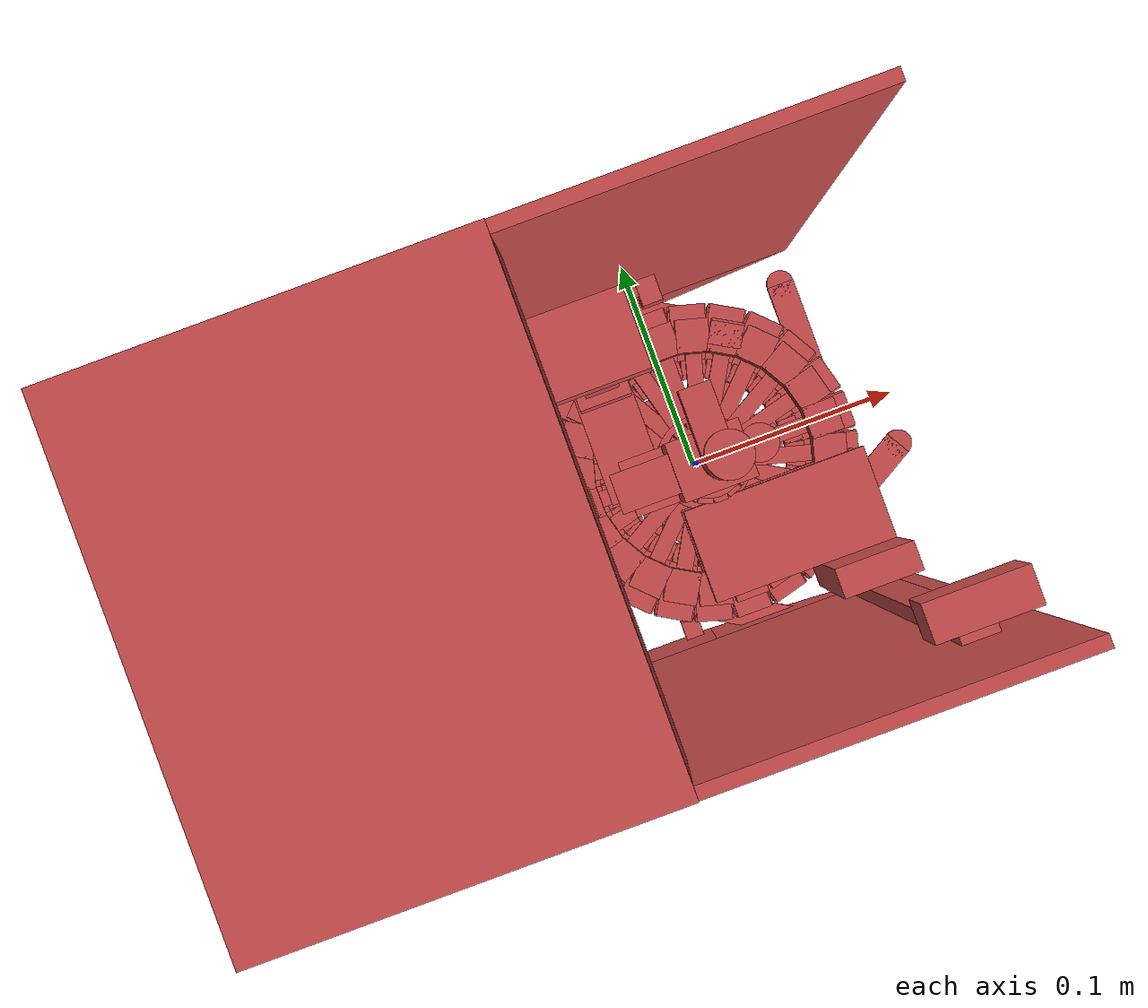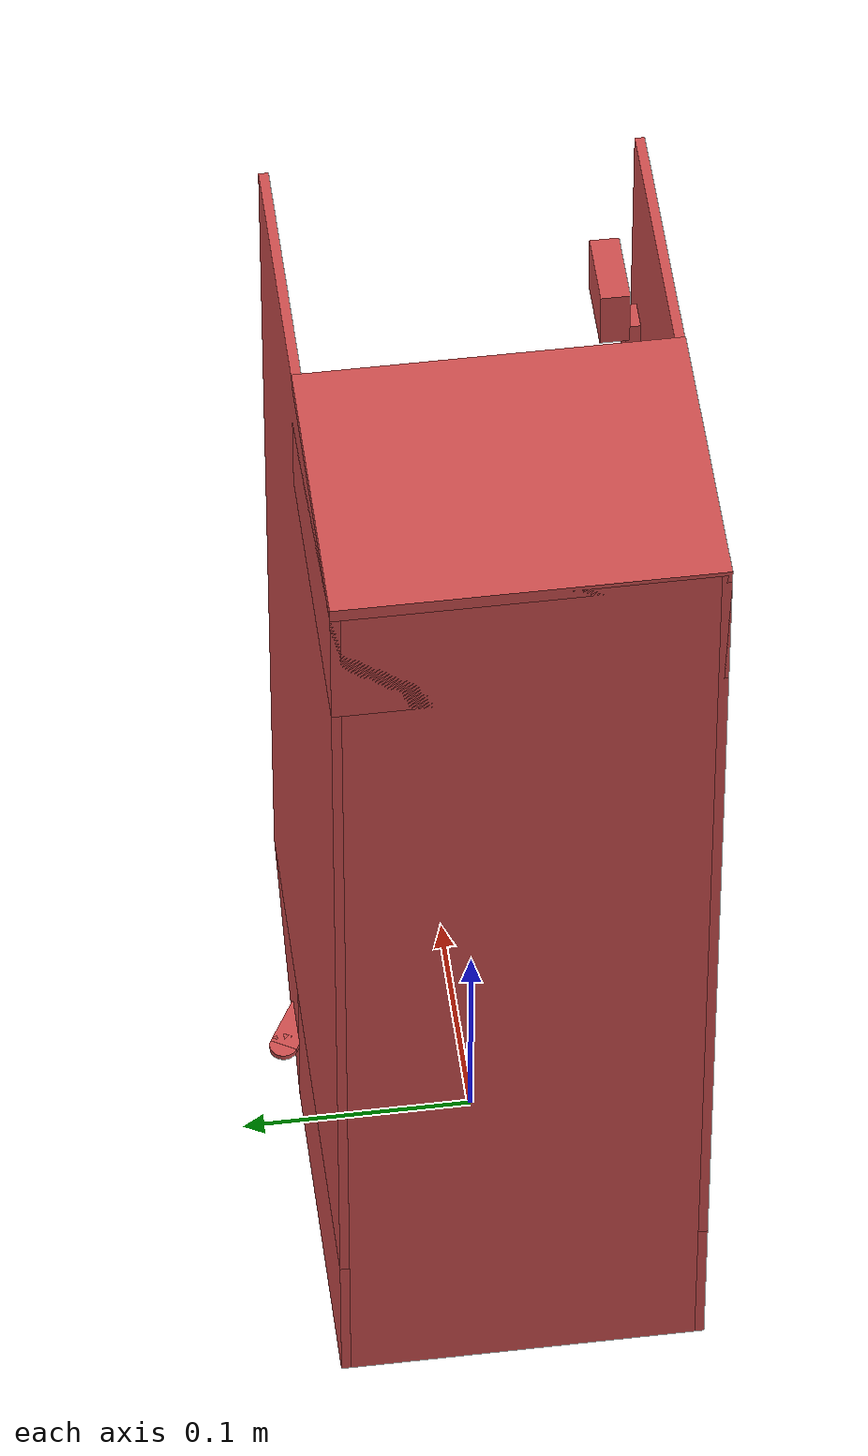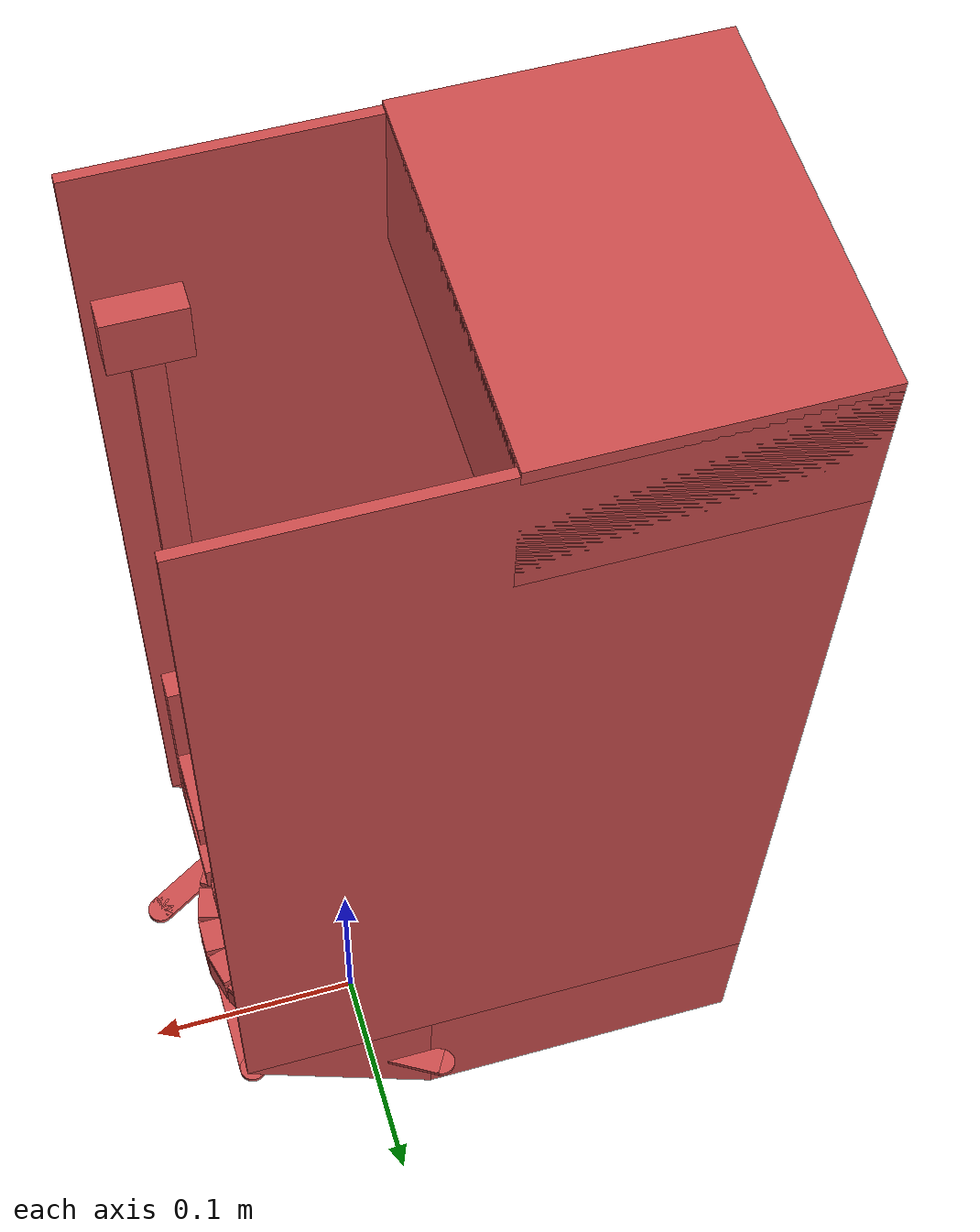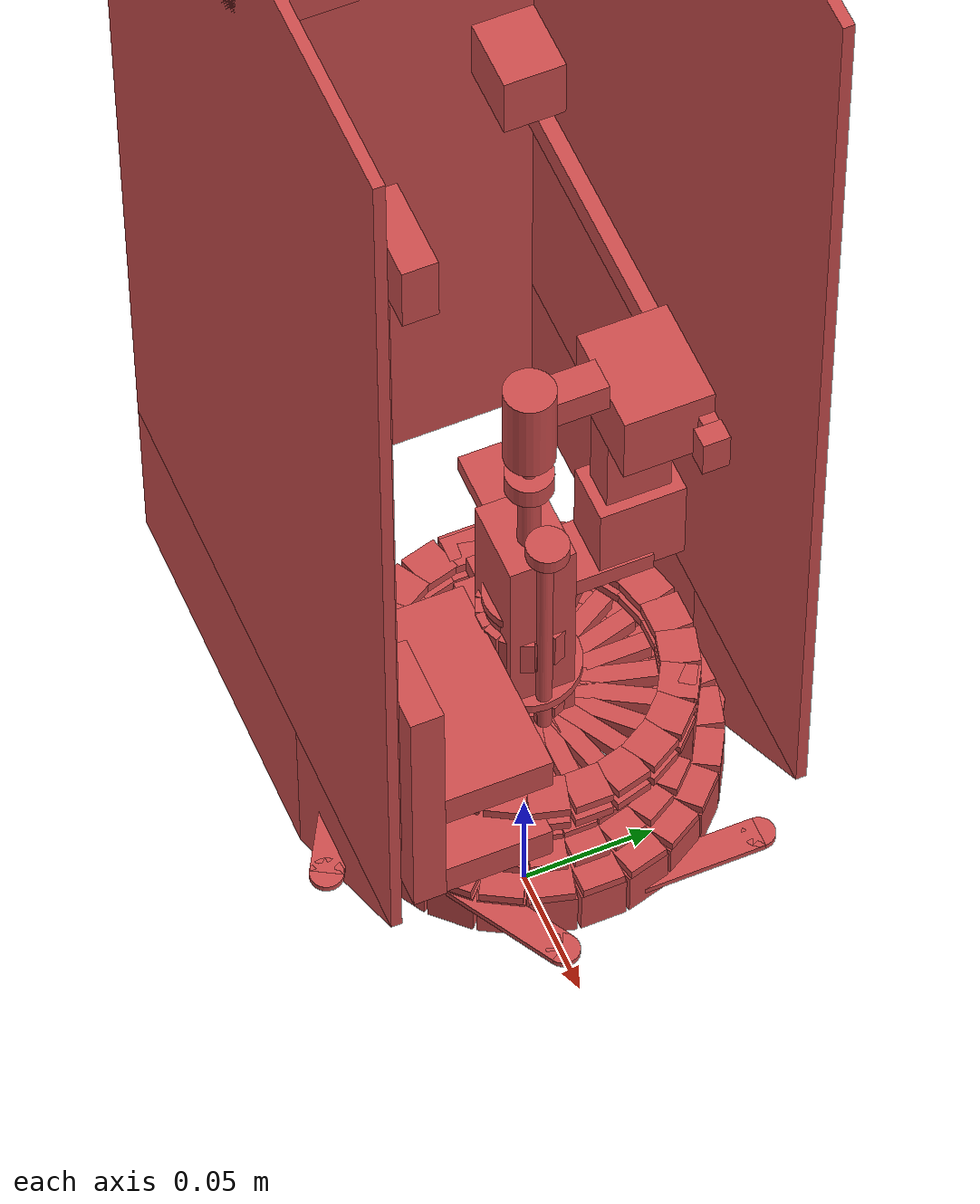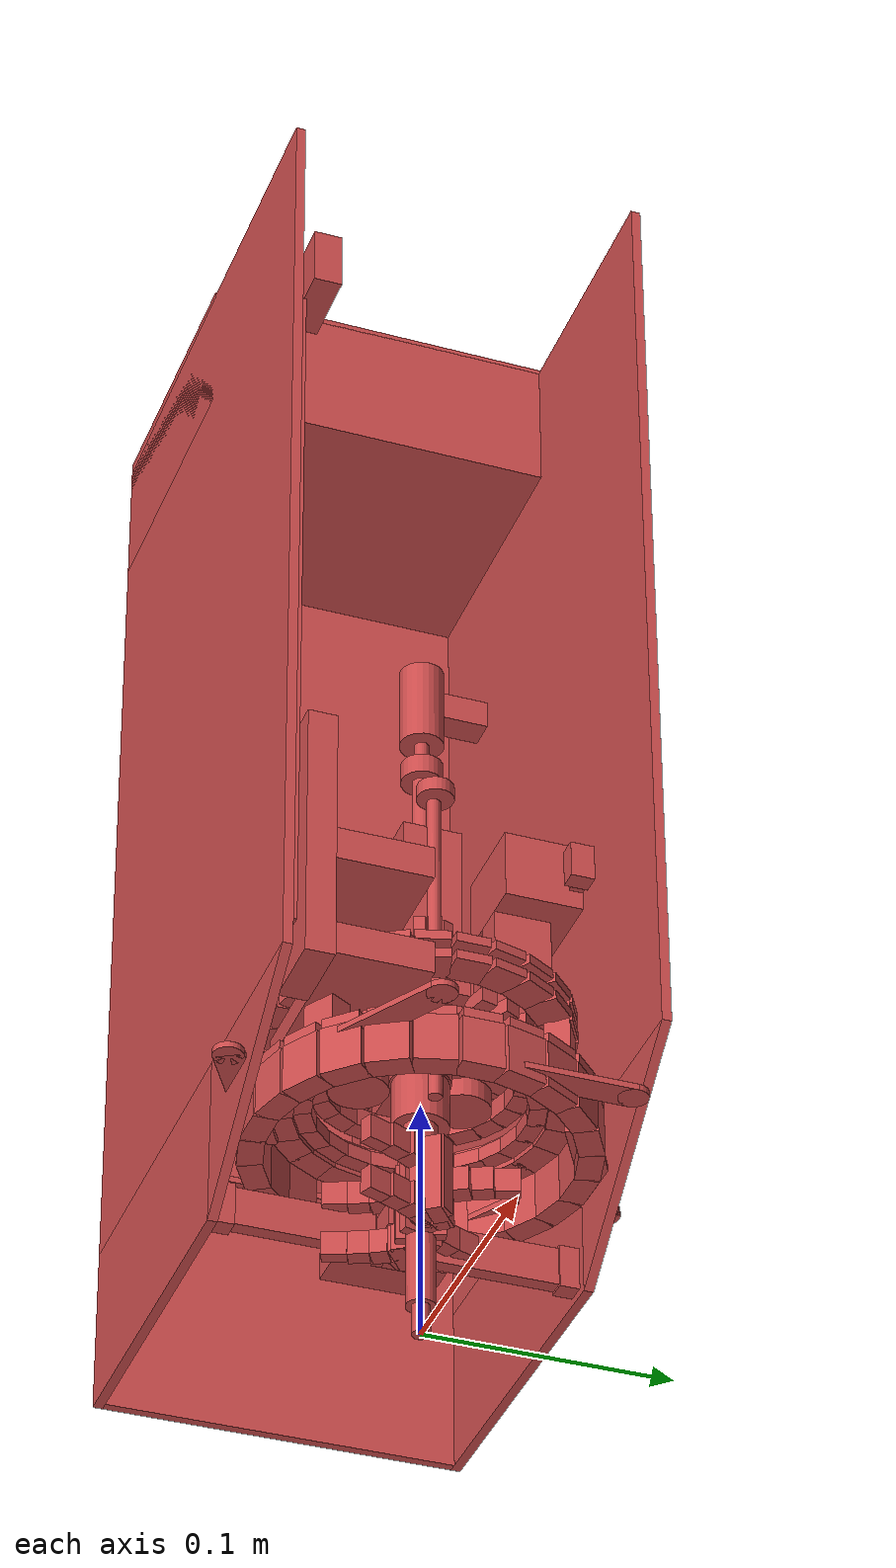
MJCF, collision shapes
<mujoco model="vertical_hand">
  <!-- Generated by scripts/generate_vertical_hand_blend.py from scripts/vertical_hand_rig.py; do not edit by hand. -->
  <compiler angle="radian" meshdir="meshes" autolimits="true"/>
  <default>
    <equality solref="0.005 1"/>   <!-- the followers stay within a few milliradians of their leader -->
  </default>

  <asset>
    <material name="black" rgba="0.12 0.13 0.15 1" specular="0.5" shininess="0.25"/>
    <material name="blue" rgba="0.41 0.58 0.87 1" specular="0.5" shininess="0.25"/>
    <material name="bolt" rgba="0.2 0.21 0.23 1" specular="0.5" shininess="0.25"/>
    <material name="dark" rgba="0.06 0.06 0.07 1" specular="0.5" shininess="0.25"/>
    <material name="display" rgba="0.02 0.02 0.02 1" specular="0.5" shininess="0.25"/>
    <material name="gold" rgba="0.83 0.65 0.24 1" specular="0.5" shininess="0.25"/>
    <material name="gray" rgba="0.4627 0.49 0.53 1" specular="0.5" shininess="0.25"/>
    <material name="housing" rgba="0.09 0.1 0.11 1" specular="0.5" shininess="0.25"/>
    <material name="led" rgba="0.21 0.76 0.42 1" specular="0.5" shininess="0.25"/>
    <material name="liner" rgba="0.13 0.14 0.16 1" specular="0.5" shininess="0.25"/>
    <material name="steel" rgba="0.75 0.76 0.78 1" specular="0.5" shininess="0.25"/>
    <material name="white" rgba="0.93 0.93 0.92 1" specular="0.5" shininess="0.25"/>
    <mesh name="hand__black" file="hand__black.stl"/>
    <mesh name="hand__gray" file="hand__gray.stl"/>
    <mesh name="hand__housing" file="hand__housing.stl"/>
    <mesh name="hand__led" file="hand__led.stl"/>
    <mesh name="hand__steel" file="hand__steel.stl"/>
    <mesh name="jaw_l__black" file="jaw_l__black.stl"/>
    <mesh name="jaw_l__bolt" file="jaw_l__bolt.stl"/>
    <mesh name="jaw_l__gray" file="jaw_l__gray.stl"/>
    <mesh name="jaw_l__liner" file="jaw_l__liner.stl"/>
    <mesh name="jaw_r__black" file="jaw_r__black.stl"/>
    <mesh name="jaw_r__bolt" file="jaw_r__bolt.stl"/>
    <mesh name="jaw_r__gray" file="jaw_r__gray.stl"/>
    <mesh name="jaw_r__liner" file="jaw_r__liner.stl"/>
    <mesh name="clamp_slide__black" file="clamp_slide__black.stl"/>
    <mesh name="clamp_slide__gray" file="clamp_slide__gray.stl"/>
    <mesh name="clamp_lift__black" file="clamp_lift__black.stl"/>
    <mesh name="clamp_lift__gray" file="clamp_lift__gray.stl"/>
    <mesh name="clamp_lift__housing" file="clamp_lift__housing.stl"/>
    <mesh name="housing__gray" file="housing__gray.stl"/>
    <mesh name="housing__housing" file="housing__housing.stl"/>
    <mesh name="housing__steel" file="housing__steel.stl"/>
    <mesh name="cam__gold" file="cam__gold.stl"/>
    <mesh name="sun__gold" file="sun__gold.stl"/>
    <mesh name="sun__steel" file="sun__steel.stl"/>
    <mesh name="planet_0__housing" file="planet_0__housing.stl"/>
    <mesh name="planet_1__housing" file="planet_1__housing.stl"/>
    <mesh name="planet_2__housing" file="planet_2__housing.stl"/>
    <mesh name="blade_0__gold" file="blade_0__gold.stl"/>
    <mesh name="blade_1__gold" file="blade_1__gold.stl"/>
    <mesh name="blade_2__gold" file="blade_2__gold.stl"/>
    <mesh name="blade_3__gold" file="blade_3__gold.stl"/>
    <mesh name="blade_4__gold" file="blade_4__gold.stl"/>
    <mesh name="blade_5__gold" file="blade_5__gold.stl"/>
    <mesh name="pip_slide__blue" file="pip_slide__blue.stl"/>
    <mesh name="pip_slide__dark" file="pip_slide__dark.stl"/>
    <mesh name="pip_slide__display" file="pip_slide__display.stl"/>
    <mesh name="pip_slide__gray" file="pip_slide__gray.stl"/>
    <mesh name="pip_slide__housing" file="pip_slide__housing.stl"/>
    <mesh name="pip_slide__white" file="pip_slide__white.stl"/>
    <mesh name="plunger__blue" file="plunger__blue.stl"/>
    <mesh name="plunger__steel" file="plunger__steel.stl"/>
    <mesh name="plunger__white" file="plunger__white.stl"/>
    <mesh name="col_hand_14" file="col_hand_14.stl"/>
    <mesh name="col_hand_17" file="col_hand_17.stl"/>
  </asset>

  <worldbody>
    <body name="vertical_hand">
      <body name="approach" pos="0 0 0">
        <inertial pos="0 0 0" mass="0.5" diaginertia="0.0001 0.0001 0.0001"/>
        <joint name="approach" type="slide" axis="1 0 0" range="-0.2 0.05" armature="0.001" damping="0.5"/>
        <body name="hand" pos="0 0 0">
          <inertial pos="0 0 0" mass="3" diaginertia="0.0006 0.0006 0.0006"/>
          <joint name="lift" type="slide" axis="0 0 1" range="0 0.3" armature="0.001" damping="0.5"/>
          <geom name="hand__black" type="mesh" mesh="hand__black" material="black" contype="0" conaffinity="0" group="2" mass="0"/>
          <geom name="hand__gray" type="mesh" mesh="hand__gray" material="gray" contype="0" conaffinity="0" group="2" mass="0"/>
          <geom name="hand__housing" type="mesh" mesh="hand__housing" material="housing" contype="0" conaffinity="0" group="2" mass="0"/>
          <geom name="hand__led" type="mesh" mesh="hand__led" material="led" contype="0" conaffinity="0" group="2" mass="0"/>
          <geom name="hand__steel" type="mesh" mesh="hand__steel" material="steel" contype="0" conaffinity="0" group="2" mass="0"/>
          <geom name="hand_col_0" type="box" pos="-0.165 0 0.28755" size="0.002 0.073 0.24245" contype="1" conaffinity="42" group="3" rgba="0.8 0.3 0.3 0.3" mass="0"/>
          <geom name="hand_col_1" type="box" pos="-0.028 0 0.0571" size="0.003 0.073 0.008" contype="1" conaffinity="42" group="3" rgba="0.8 0.3 0.3 0.3" mass="0"/>
          <geom name="hand_col_2" type="box" pos="-0.028 0.069 0.0571" size="0.004 0.004 0.009" contype="1" conaffinity="42" group="3" rgba="0.8 0.3 0.3 0.3" mass="0"/>
          <geom name="hand_col_3" type="box" pos="-0.028 -0.069 0.0571" size="0.004 0.004 0.009" contype="1" conaffinity="42" group="3" rgba="0.8 0.3 0.3 0.3" mass="0"/>
          <geom name="hand_col_4" type="box" pos="-0.08 0.07 0.23" size="0.08 0.003 0.006" contype="1" conaffinity="42" group="3" rgba="0.8 0.3 0.3 0.3" mass="0"/>
          <geom name="hand_col_5" type="box" pos="-0.159 0.068 0.23" size="0.004 0.005 0.008" contype="1" conaffinity="42" group="3" rgba="0.8 0.3 0.3 0.3" mass="0"/>
          <geom name="hand_col_6" type="box" pos="-0.001 0.068 0.23" size="0.004 0.005 0.008" contype="1" conaffinity="42" group="3" rgba="0.8 0.3 0.3 0.3" mass="0"/>
          <geom name="hand_col_7" type="box" pos="-0.149 0.0615 0.263" size="0.014 0.0115 0.013" contype="1" conaffinity="42" group="3" rgba="0.8 0.3 0.3 0.3" mass="0"/>
          <geom name="hand_col_8" type="box" pos="-0.042 0 0.0571" size="0.01 0.022 0.008" contype="1" conaffinity="42" group="3" rgba="0.8 0.3 0.3 0.3" mass="0"/>
          <geom name="hand_col_9" type="box" pos="-0.106 0 0.529" size="0.061 0.077 0.003" contype="1" conaffinity="42" group="3" rgba="0.8 0.3 0.3 0.3" mass="0"/>
          <geom name="hand_col_10" type="box" pos="0.045 -0.07 0.2928" size="0.006 0.003 0.1558" contype="1" conaffinity="42" group="3" rgba="0.8 0.3 0.3 0.3" mass="0"/>
          <geom name="hand_col_11" type="box" pos="0.045 -0.061 0.4646" size="0.016 0.006 0.013" contype="1" conaffinity="42" group="3" rgba="0.8 0.3 0.3 0.3" mass="0"/>
          <geom name="hand_col_12" type="box" pos="-0.051 0.075 0.3225" size="0.116 0.002 0.2075" contype="1" conaffinity="42" group="3" rgba="0.8 0.3 0.3 0.3" mass="0"/>
          <geom name="hand_col_13" type="box" pos="-0.0935 0.075 0.08005" size="0.0735 0.002 0.03495" contype="1" conaffinity="42" group="3" rgba="0.8 0.3 0.3 0.3" mass="0"/>
          <geom name="hand_col_14" type="mesh" mesh="col_hand_14" contype="1" conaffinity="42" group="3" rgba="0.8 0.3 0.3 0.3" mass="0"/>
          <geom name="hand_col_15" type="box" pos="-0.051 -0.075 0.3225" size="0.116 0.002 0.2075" contype="1" conaffinity="42" group="3" rgba="0.8 0.3 0.3 0.3" mass="0"/>
          <geom name="hand_col_16" type="box" pos="-0.0935 -0.075 0.08005" size="0.0735 0.002 0.03495" contype="1" conaffinity="42" group="3" rgba="0.8 0.3 0.3 0.3" mass="0"/>
          <geom name="hand_col_17" type="mesh" mesh="col_hand_17" contype="1" conaffinity="42" group="3" rgba="0.8 0.3 0.3 0.3" mass="0"/>
          <geom name="hand_col_18" type="box" pos="-0.106 0 0.5" size="0.061 0.077 0.03" contype="1" conaffinity="42" group="3" rgba="0.8 0.3 0.3 0.3" mass="0"/>
          <body name="jaw_l" pos="0 0 0.0571">
            <inertial pos="0 0 0" mass="0.12" diaginertia="2.4e-05 2.4e-05 2.4e-05"/>
            <joint name="jaw_l" type="slide" axis="0 1 0" range="0.0117763 0.0613506" armature="0.001" damping="0.5"/>
            <geom name="jaw_l__black" type="mesh" mesh="jaw_l__black" material="black" contype="0" conaffinity="0" group="2" mass="0"/>
            <geom name="jaw_l__bolt" type="mesh" mesh="jaw_l__bolt" material="bolt" contype="0" conaffinity="0" group="2" mass="0"/>
            <geom name="jaw_l__gray" type="mesh" mesh="jaw_l__gray" material="gray" contype="0" conaffinity="0" group="2" mass="0"/>
            <geom name="jaw_l__liner" type="mesh" mesh="jaw_l__liner" material="liner" contype="0" conaffinity="0" group="2" mass="0"/>
            <geom name="jaw_l_col_0" type="box" pos="-0.027 0.002 0" size="0.003 0.007 0.012" contype="1" conaffinity="42" group="3" rgba="0.8 0.3 0.3 0.3" mass="0"/>
            <geom name="jaw_l_col_1" type="box" pos="-0.0160517 -0.00165861 0" quat="0.901303 0 0 0.433189" size="0.00320156 0.007625 0.016" contype="1" conaffinity="42" group="3" rgba="0.8 0.3 0.3 0.3" mass="0"/>
            <geom name="jaw_l_col_2" type="box" pos="-0.00945 0.0021 0" quat="0.948683 0 0 0.316228" size="0.0025 0.005625 0.016" contype="1" conaffinity="42" group="3" rgba="0.8 0.3 0.3 0.3" mass="0"/>
            <geom name="jaw_l_col_3" type="box" pos="-0.00315204 0.00410818 0" quat="0.992508 0 0 0.122183" size="0.00206155 0.004625 0.016" contype="1" conaffinity="42" group="3" rgba="0.8 0.3 0.3 0.3" mass="0"/>
            <geom name="jaw_l_col_4" type="box" pos="0.00315204 0.00410818 0" quat="0.992508 0 0 -0.122183" size="0.00206155 0.004625 0.016" contype="1" conaffinity="42" group="3" rgba="0.8 0.3 0.3 0.3" mass="0"/>
            <geom name="jaw_l_col_5" type="box" pos="0.00945 0.0021 0" quat="0.948683 0 0 -0.316228" size="0.0025 0.005625 0.016" contype="1" conaffinity="42" group="3" rgba="0.8 0.3 0.3 0.3" mass="0"/>
            <geom name="jaw_l_col_6" type="box" pos="0.0160517 -0.00165861 0" quat="0.901303 0 0 -0.433189" size="0.00320156 0.007625 0.016" contype="1" conaffinity="42" group="3" rgba="0.8 0.3 0.3 0.3" mass="0"/>
            <geom name="jaw_l_col_7" type="box" pos="0.0174342 -0.00986429 -0.011" quat="0.86686 0 0 -0.498551" size="0.00347986 0.00416667 0.005" contype="1" conaffinity="42" group="3" rgba="0.8 0.3 0.3 0.3" mass="0"/>
            <geom name="jaw_l_col_8" type="box" pos="0.020512 -0.0172763 -0.011" quat="0.84283 0 0 -0.53818" size="0.00415949 0.0035 0.005" contype="1" conaffinity="42" group="3" rgba="0.8 0.3 0.3 0.3" mass="0"/>
            <geom name="jaw_l_col_9" type="box" pos="0.023483 -0.0260479 -0.011" quat="0.82454 0 0 -0.565804" size="0.00486473 0.00283333 0.005" contype="1" conaffinity="42" group="3" rgba="0.8 0.3 0.3 0.3" mass="0"/>
            <geom name="jaw_l_col_10" type="box" pos="-0.023483 -0.0260479 -0.011" quat="0.82454 0 0 0.565804" size="0.00486473 0.00283333 0.005" contype="1" conaffinity="42" group="3" rgba="0.8 0.3 0.3 0.3" mass="0"/>
            <geom name="jaw_l_col_11" type="box" pos="-0.020512 -0.0172763 -0.011" quat="0.84283 0 0 0.53818" size="0.00415949 0.0035 0.005" contype="1" conaffinity="42" group="3" rgba="0.8 0.3 0.3 0.3" mass="0"/>
            <geom name="jaw_l_col_12" type="box" pos="-0.0174342 -0.00986429 -0.011" quat="0.86686 0 0 0.498551" size="0.00347986 0.00416667 0.005" contype="1" conaffinity="42" group="3" rgba="0.8 0.3 0.3 0.3" mass="0"/>
            <geom name="jaw_l_col_13" type="box" pos="0.0174342 -0.00986429 0.011" quat="0.86686 0 0 -0.498551" size="0.00347986 0.00416667 0.005" contype="1" conaffinity="42" group="3" rgba="0.8 0.3 0.3 0.3" mass="0"/>
            <geom name="jaw_l_col_14" type="box" pos="0.020512 -0.0172763 0.011" quat="0.84283 0 0 -0.53818" size="0.00415949 0.0035 0.005" contype="1" conaffinity="42" group="3" rgba="0.8 0.3 0.3 0.3" mass="0"/>
            <geom name="jaw_l_col_15" type="box" pos="0.023483 -0.0260479 0.011" quat="0.82454 0 0 -0.565804" size="0.00486473 0.00283333 0.005" contype="1" conaffinity="42" group="3" rgba="0.8 0.3 0.3 0.3" mass="0"/>
            <geom name="jaw_l_col_16" type="box" pos="-0.023483 -0.0260479 0.011" quat="0.82454 0 0 0.565804" size="0.00486473 0.00283333 0.005" contype="1" conaffinity="42" group="3" rgba="0.8 0.3 0.3 0.3" mass="0"/>
            <geom name="jaw_l_col_17" type="box" pos="-0.020512 -0.0172763 0.011" quat="0.84283 0 0 0.53818" size="0.00415949 0.0035 0.005" contype="1" conaffinity="42" group="3" rgba="0.8 0.3 0.3 0.3" mass="0"/>
            <geom name="jaw_l_col_18" type="box" pos="-0.0174342 -0.00986429 0.011" quat="0.86686 0 0 0.498551" size="0.00347986 0.00416667 0.005" contype="1" conaffinity="42" group="3" rgba="0.8 0.3 0.3 0.3" mass="0"/>
            <geom name="jaw_l_col_19" type="box" pos="-0.017 0.006 -0.011" size="0.007 0.003 0.005" contype="1" conaffinity="42" group="3" rgba="0.8 0.3 0.3 0.3" mass="0"/>
            <geom name="jaw_l_col_20" type="box" pos="-0.017 0.006 0.011" size="0.007 0.003 0.005" contype="1" conaffinity="42" group="3" rgba="0.8 0.3 0.3 0.3" mass="0"/>
            <site name="jaw_l_vertex" pos="0 0 0" size="0.003" rgba="0.9 0.3 0.1 0.5" group="4"/>
          </body>
          <body name="jaw_r" pos="0 0 0.0571">
            <inertial pos="0 0 0" mass="0.12" diaginertia="2.4e-05 2.4e-05 2.4e-05"/>
            <joint name="jaw_r" type="slide" axis="0 -1 0" range="0.0117763 0.0613506" armature="1e-05" damping="0.01"/>
            <geom name="jaw_r__black" type="mesh" mesh="jaw_r__black" material="black" contype="0" conaffinity="0" group="2" mass="0"/>
            <geom name="jaw_r__bolt" type="mesh" mesh="jaw_r__bolt" material="bolt" contype="0" conaffinity="0" group="2" mass="0"/>
            <geom name="jaw_r__gray" type="mesh" mesh="jaw_r__gray" material="gray" contype="0" conaffinity="0" group="2" mass="0"/>
            <geom name="jaw_r__liner" type="mesh" mesh="jaw_r__liner" material="liner" contype="0" conaffinity="0" group="2" mass="0"/>
            <geom name="jaw_r_col_0" type="box" pos="-0.027 -0.002 0" size="0.003 0.007 0.012" contype="1" conaffinity="42" group="3" rgba="0.8 0.3 0.3 0.3" mass="0"/>
            <geom name="jaw_r_col_1" type="box" pos="-0.0160517 0.00165861 0" quat="0.901303 0 0 -0.433189" size="0.00320156 0.007625 0.016" contype="1" conaffinity="42" group="3" rgba="0.8 0.3 0.3 0.3" mass="0"/>
            <geom name="jaw_r_col_2" type="box" pos="-0.00945 -0.0021 0" quat="0.948683 0 0 -0.316228" size="0.0025 0.005625 0.016" contype="1" conaffinity="42" group="3" rgba="0.8 0.3 0.3 0.3" mass="0"/>
            <geom name="jaw_r_col_3" type="box" pos="-0.00315204 -0.00410818 0" quat="0.992508 0 0 -0.122183" size="0.00206155 0.004625 0.016" contype="1" conaffinity="42" group="3" rgba="0.8 0.3 0.3 0.3" mass="0"/>
            <geom name="jaw_r_col_4" type="box" pos="0.00315204 -0.00410818 0" quat="0.992508 0 0 0.122183" size="0.00206155 0.004625 0.016" contype="1" conaffinity="42" group="3" rgba="0.8 0.3 0.3 0.3" mass="0"/>
            <geom name="jaw_r_col_5" type="box" pos="0.00945 -0.0021 0" quat="0.948683 0 0 0.316228" size="0.0025 0.005625 0.016" contype="1" conaffinity="42" group="3" rgba="0.8 0.3 0.3 0.3" mass="0"/>
            <geom name="jaw_r_col_6" type="box" pos="0.0160517 0.00165861 0" quat="0.901303 0 0 0.433189" size="0.00320156 0.007625 0.016" contype="1" conaffinity="42" group="3" rgba="0.8 0.3 0.3 0.3" mass="0"/>
            <geom name="jaw_r_col_7" type="box" pos="0.0174342 0.00986429 0" quat="0.86686 0 0 0.498551" size="0.00347986 0.00416667 0.005" contype="1" conaffinity="42" group="3" rgba="0.8 0.3 0.3 0.3" mass="0"/>
            <geom name="jaw_r_col_8" type="box" pos="0.020512 0.0172763 0" quat="0.84283 0 0 0.53818" size="0.00415949 0.0035 0.005" contype="1" conaffinity="42" group="3" rgba="0.8 0.3 0.3 0.3" mass="0"/>
            <geom name="jaw_r_col_9" type="box" pos="0.023483 0.0260479 0" quat="0.82454 0 0 0.565804" size="0.00486473 0.00283333 0.005" contype="1" conaffinity="42" group="3" rgba="0.8 0.3 0.3 0.3" mass="0"/>
            <geom name="jaw_r_col_10" type="box" pos="-0.023483 0.0260479 0" quat="0.82454 0 0 -0.565804" size="0.00486473 0.00283333 0.005" contype="1" conaffinity="42" group="3" rgba="0.8 0.3 0.3 0.3" mass="0"/>
            <geom name="jaw_r_col_11" type="box" pos="-0.020512 0.0172763 0" quat="0.84283 0 0 -0.53818" size="0.00415949 0.0035 0.005" contype="1" conaffinity="42" group="3" rgba="0.8 0.3 0.3 0.3" mass="0"/>
            <geom name="jaw_r_col_12" type="box" pos="-0.0174342 0.00986429 0" quat="0.86686 0 0 -0.498551" size="0.00347986 0.00416667 0.005" contype="1" conaffinity="42" group="3" rgba="0.8 0.3 0.3 0.3" mass="0"/>
            <geom name="jaw_r_col_13" type="box" pos="-0.017 -0.006 0" size="0.007 0.003 0.005" contype="1" conaffinity="42" group="3" rgba="0.8 0.3 0.3 0.3" mass="0"/>
            <site name="jaw_r_vertex" pos="0 0 0" size="0.003" rgba="0.9 0.3 0.1 0.5" group="4"/>
          </body>
          <body name="clamp_slide" pos="0 0 0">
            <inertial pos="0 0 0" mass="0.3" diaginertia="6e-05 6e-05 6e-05"/>
            <joint name="clamp_x" type="slide" axis="1 0 0" range="-0.1 0" armature="0.001" damping="0.5"/>
            <geom name="clamp_slide__black" type="mesh" mesh="clamp_slide__black" material="black" contype="0" conaffinity="0" group="2" mass="0"/>
            <geom name="clamp_slide__gray" type="mesh" mesh="clamp_slide__gray" material="gray" contype="0" conaffinity="0" group="2" mass="0"/>
            <geom name="clamp_slide_col_0" type="box" pos="-0.03 0.0565 0.231" size="0.02 0.0165 0.015" contype="1" conaffinity="42" group="3" rgba="0.8 0.3 0.3 0.3" mass="0"/>
            <geom name="clamp_slide_col_1" type="box" pos="-0.03 0.052 0.1798" size="0.007 0.012 0.0362" contype="1" conaffinity="42" group="3" rgba="0.8 0.3 0.3 0.3" mass="0"/>
            <body name="clamp_lift" pos="0 0 0.0796">
              <inertial pos="0 0 0" mass="0.35" diaginertia="7e-05 7e-05 7e-05"/>
              <joint name="clamp_lift" type="slide" axis="0 0 1" range="0 0.0355" armature="0.001" damping="0.5"/>
              <geom name="clamp_lift__black" type="mesh" mesh="clamp_lift__black" material="black" contype="0" conaffinity="0" group="2" mass="0"/>
              <geom name="clamp_lift__gray" type="mesh" mesh="clamp_lift__gray" material="gray" contype="0" conaffinity="0" group="2" mass="0"/>
              <geom name="clamp_lift__housing" type="mesh" mesh="clamp_lift__housing" material="housing" contype="0" conaffinity="0" group="2" mass="0"/>
              <geom name="clamp_lift_col_0" type="box" pos="-0.017 0 0.066" size="0.017 0.012 0.004" contype="1" conaffinity="42" group="3" rgba="0.8 0.3 0.3 0.3" mass="0"/>
              <geom name="clamp_lift_col_1" type="box" pos="-0.03 0.026 0.066" size="0.012 0.03 0.004" contype="1" conaffinity="42" group="3" rgba="0.8 0.3 0.3 0.3" mass="0"/>
              <geom name="clamp_lift_col_2" type="box" pos="-0.03 0.052 0.083" size="0.011 0.016 0.019" contype="1" conaffinity="42" group="3" rgba="0.8 0.3 0.3 0.3" mass="0"/>
              <geom name="clamp_lift_col_3" type="cylinder" pos="0 0 0.062" size="0.02 0.002" contype="1" conaffinity="42" group="3" rgba="0.8 0.3 0.3 0.3" mass="0"/>
              <geom name="clamp_lift_col_4" type="cylinder" pos="0 0 0.087" size="0.014 0.017" contype="1" conaffinity="42" group="3" rgba="0.8 0.3 0.3 0.3" mass="0"/>
              <geom name="clamp_lift_col_5" type="cylinder" pos="0 0 0.104" size="0.015 0.002" contype="1" conaffinity="42" group="3" rgba="0.8 0.3 0.3 0.3" mass="0"/>
              <body name="housing" pos="0 0 0">
                <inertial pos="0 0 0" mass="0.3" diaginertia="6e-05 6e-05 6e-05"/>
                <joint name="body_yaw" type="hinge" axis="0 0 1" range="0 15.708" armature="0.001" damping="0.02"/>
                <geom name="housing__gray" type="mesh" mesh="housing__gray" material="gray" contype="0" conaffinity="0" group="2" mass="0"/>
                <geom name="housing__housing" type="mesh" mesh="housing__housing" material="housing" contype="0" conaffinity="0" group="2" mass="0"/>
                <geom name="housing__steel" type="mesh" mesh="housing__steel" material="steel" contype="0" conaffinity="0" group="2" mass="0"/>
                <geom name="housing_col_0" type="box" pos="0.026 0 0.045" size="0.02 0.00342296 0.003" contype="1" conaffinity="42" group="3" rgba="0.8 0.3 0.3 0.3" mass="0"/>
                <geom name="housing_col_1" type="box" pos="0.0251141 0.0067293 0.045" quat="0.991445 0 0 0.130526" size="0.02 0.00342296 0.003" contype="1" conaffinity="42" group="3" rgba="0.8 0.3 0.3 0.3" mass="0"/>
                <geom name="housing_col_2" type="box" pos="0.0225167 0.013 0.045" quat="0.965926 0 0 0.258819" size="0.02 0.00342296 0.003" contype="1" conaffinity="42" group="3" rgba="0.8 0.3 0.3 0.3" mass="0"/>
                <geom name="housing_col_3" type="box" pos="0.0183848 0.0183848 0.045" quat="0.92388 0 0 0.382683" size="0.02 0.00342296 0.003" contype="1" conaffinity="42" group="3" rgba="0.8 0.3 0.3 0.3" mass="0"/>
                <geom name="housing_col_4" type="box" pos="0.013 0.0225167 0.045" quat="0.866025 0 0 0.5" size="0.02 0.00342296 0.003" contype="1" conaffinity="42" group="3" rgba="0.8 0.3 0.3 0.3" mass="0"/>
                <geom name="housing_col_5" type="box" pos="0.0067293 0.0251141 0.045" quat="0.793353 0 0 0.608761" size="0.02 0.00342296 0.003" contype="1" conaffinity="42" group="3" rgba="0.8 0.3 0.3 0.3" mass="0"/>
                <geom name="housing_col_6" type="box" pos="1.59204e-18 0.026 0.045" quat="0.707107 0 0 0.707107" size="0.02 0.00342296 0.003" contype="1" conaffinity="42" group="3" rgba="0.8 0.3 0.3 0.3" mass="0"/>
                <geom name="housing_col_7" type="box" pos="-0.0067293 0.0251141 0.045" quat="0.608761 0 0 0.793353" size="0.02 0.00342296 0.003" contype="1" conaffinity="42" group="3" rgba="0.8 0.3 0.3 0.3" mass="0"/>
                <geom name="housing_col_8" type="box" pos="-0.013 0.0225167 0.045" quat="0.5 0 0 0.866025" size="0.02 0.00342296 0.003" contype="1" conaffinity="42" group="3" rgba="0.8 0.3 0.3 0.3" mass="0"/>
                <geom name="housing_col_9" type="box" pos="-0.0183848 0.0183848 0.045" quat="0.382683 0 0 0.92388" size="0.02 0.00342296 0.003" contype="1" conaffinity="42" group="3" rgba="0.8 0.3 0.3 0.3" mass="0"/>
                <geom name="housing_col_10" type="box" pos="-0.0225167 0.013 0.045" quat="0.258819 0 0 0.965926" size="0.02 0.00342296 0.003" contype="1" conaffinity="42" group="3" rgba="0.8 0.3 0.3 0.3" mass="0"/>
                <geom name="housing_col_11" type="box" pos="-0.0251141 0.0067293 0.045" quat="0.130526 0 0 0.991445" size="0.02 0.00342296 0.003" contype="1" conaffinity="42" group="3" rgba="0.8 0.3 0.3 0.3" mass="0"/>
                <geom name="housing_col_12" type="box" pos="-0.026 3.18408e-18 0.045" quat="4.37114e-08 0 0 1" size="0.02 0.00342296 0.003" contype="1" conaffinity="42" group="3" rgba="0.8 0.3 0.3 0.3" mass="0"/>
                <geom name="housing_col_13" type="box" pos="-0.0251141 -0.0067293 0.045" quat="0.130526 -0 -0 -0.991445" size="0.02 0.00342296 0.003" contype="1" conaffinity="42" group="3" rgba="0.8 0.3 0.3 0.3" mass="0"/>
                <geom name="housing_col_14" type="box" pos="-0.0225167 -0.013 0.045" quat="0.258819 -0 -0 -0.965926" size="0.02 0.00342296 0.003" contype="1" conaffinity="42" group="3" rgba="0.8 0.3 0.3 0.3" mass="0"/>
                <geom name="housing_col_15" type="box" pos="-0.0183848 -0.0183848 0.045" quat="0.382683 -0 -0 -0.92388" size="0.02 0.00342296 0.003" contype="1" conaffinity="42" group="3" rgba="0.8 0.3 0.3 0.3" mass="0"/>
                <geom name="housing_col_16" type="box" pos="-0.013 -0.0225167 0.045" quat="0.5 -0 -0 -0.866025" size="0.02 0.00342296 0.003" contype="1" conaffinity="42" group="3" rgba="0.8 0.3 0.3 0.3" mass="0"/>
                <geom name="housing_col_17" type="box" pos="-0.0067293 -0.0251141 0.045" quat="0.608761 -0 -0 -0.793353" size="0.02 0.00342296 0.003" contype="1" conaffinity="42" group="3" rgba="0.8 0.3 0.3 0.3" mass="0"/>
                <geom name="housing_col_18" type="box" pos="-4.77612e-18 -0.026 0.045" quat="0.707107 0 0 -0.707107" size="0.02 0.00342296 0.003" contype="1" conaffinity="42" group="3" rgba="0.8 0.3 0.3 0.3" mass="0"/>
                <geom name="housing_col_19" type="box" pos="0.0067293 -0.0251141 0.045" quat="0.793353 0 0 -0.608762" size="0.02 0.00342296 0.003" contype="1" conaffinity="42" group="3" rgba="0.8 0.3 0.3 0.3" mass="0"/>
                <geom name="housing_col_20" type="box" pos="0.013 -0.0225167 0.045" quat="0.866025 0 0 -0.5" size="0.02 0.00342296 0.003" contype="1" conaffinity="42" group="3" rgba="0.8 0.3 0.3 0.3" mass="0"/>
                <geom name="housing_col_21" type="box" pos="0.0183848 -0.0183848 0.045" quat="0.923879 0 0 -0.382684" size="0.02 0.00342296 0.003" contype="1" conaffinity="42" group="3" rgba="0.8 0.3 0.3 0.3" mass="0"/>
                <geom name="housing_col_22" type="box" pos="0.0225167 -0.013 0.045" quat="0.965926 0 0 -0.258819" size="0.02 0.00342296 0.003" contype="1" conaffinity="42" group="3" rgba="0.8 0.3 0.3 0.3" mass="0"/>
                <geom name="housing_col_23" type="box" pos="0.0251141 -0.0067293 0.045" quat="0.991445 0 0 -0.130526" size="0.02 0.00342296 0.003" contype="1" conaffinity="42" group="3" rgba="0.8 0.3 0.3 0.3" mass="0"/>
                <geom name="housing_col_24" type="box" pos="0.053 0 0.05" size="0.007 0.00697758 0.002" contype="1" conaffinity="42" group="3" rgba="0.8 0.3 0.3 0.3" mass="0"/>
                <geom name="housing_col_25" type="box" pos="0.0511941 0.0137174 0.05" quat="0.991445 0 0 0.130526" size="0.007 0.00697758 0.002" contype="1" conaffinity="42" group="3" rgba="0.8 0.3 0.3 0.3" mass="0"/>
                <geom name="housing_col_26" type="box" pos="0.0458993 0.0265 0.05" quat="0.965926 0 0 0.258819" size="0.007 0.00697758 0.002" contype="1" conaffinity="42" group="3" rgba="0.8 0.3 0.3 0.3" mass="0"/>
                <geom name="housing_col_27" type="box" pos="0.0374767 0.0374767 0.05" quat="0.92388 0 0 0.382683" size="0.007 0.00697758 0.002" contype="1" conaffinity="42" group="3" rgba="0.8 0.3 0.3 0.3" mass="0"/>
                <geom name="housing_col_28" type="box" pos="0.0265 0.0458993 0.05" quat="0.866025 0 0 0.5" size="0.007 0.00697758 0.002" contype="1" conaffinity="42" group="3" rgba="0.8 0.3 0.3 0.3" mass="0"/>
                <geom name="housing_col_29" type="box" pos="0.0137174 0.0511941 0.05" quat="0.793353 0 0 0.608761" size="0.007 0.00697758 0.002" contype="1" conaffinity="42" group="3" rgba="0.8 0.3 0.3 0.3" mass="0"/>
                <geom name="housing_col_30" type="box" pos="3.24531e-18 0.053 0.05" quat="0.707107 0 0 0.707107" size="0.007 0.00697758 0.002" contype="1" conaffinity="42" group="3" rgba="0.8 0.3 0.3 0.3" mass="0"/>
                <geom name="housing_col_31" type="box" pos="-0.0137174 0.0511941 0.05" quat="0.608761 0 0 0.793353" size="0.007 0.00697758 0.002" contype="1" conaffinity="42" group="3" rgba="0.8 0.3 0.3 0.3" mass="0"/>
                <geom name="housing_col_32" type="box" pos="-0.0265 0.0458993 0.05" quat="0.5 0 0 0.866025" size="0.007 0.00697758 0.002" contype="1" conaffinity="42" group="3" rgba="0.8 0.3 0.3 0.3" mass="0"/>
                <geom name="housing_col_33" type="box" pos="-0.0374767 0.0374767 0.05" quat="0.382683 0 0 0.92388" size="0.007 0.00697758 0.002" contype="1" conaffinity="42" group="3" rgba="0.8 0.3 0.3 0.3" mass="0"/>
                <geom name="housing_col_34" type="box" pos="-0.0458993 0.0265 0.05" quat="0.258819 0 0 0.965926" size="0.007 0.00697758 0.002" contype="1" conaffinity="42" group="3" rgba="0.8 0.3 0.3 0.3" mass="0"/>
                <geom name="housing_col_35" type="box" pos="-0.0511941 0.0137174 0.05" quat="0.130526 0 0 0.991445" size="0.007 0.00697758 0.002" contype="1" conaffinity="42" group="3" rgba="0.8 0.3 0.3 0.3" mass="0"/>
                <geom name="housing_col_36" type="box" pos="-0.053 6.49063e-18 0.05" quat="4.37114e-08 0 0 1" size="0.007 0.00697758 0.002" contype="1" conaffinity="42" group="3" rgba="0.8 0.3 0.3 0.3" mass="0"/>
                <geom name="housing_col_37" type="box" pos="-0.0511941 -0.0137174 0.05" quat="0.130526 -0 -0 -0.991445" size="0.007 0.00697758 0.002" contype="1" conaffinity="42" group="3" rgba="0.8 0.3 0.3 0.3" mass="0"/>
                <geom name="housing_col_38" type="box" pos="-0.0458993 -0.0265 0.05" quat="0.258819 -0 -0 -0.965926" size="0.007 0.00697758 0.002" contype="1" conaffinity="42" group="3" rgba="0.8 0.3 0.3 0.3" mass="0"/>
                <geom name="housing_col_39" type="box" pos="-0.0374767 -0.0374767 0.05" quat="0.382683 -0 -0 -0.92388" size="0.007 0.00697758 0.002" contype="1" conaffinity="42" group="3" rgba="0.8 0.3 0.3 0.3" mass="0"/>
                <geom name="housing_col_40" type="box" pos="-0.0265 -0.0458993 0.05" quat="0.5 -0 -0 -0.866025" size="0.007 0.00697758 0.002" contype="1" conaffinity="42" group="3" rgba="0.8 0.3 0.3 0.3" mass="0"/>
                <geom name="housing_col_41" type="box" pos="-0.0137174 -0.0511941 0.05" quat="0.608761 -0 -0 -0.793353" size="0.007 0.00697758 0.002" contype="1" conaffinity="42" group="3" rgba="0.8 0.3 0.3 0.3" mass="0"/>
                <geom name="housing_col_42" type="box" pos="-9.73594e-18 -0.053 0.05" quat="0.707107 0 0 -0.707107" size="0.007 0.00697758 0.002" contype="1" conaffinity="42" group="3" rgba="0.8 0.3 0.3 0.3" mass="0"/>
                <geom name="housing_col_43" type="box" pos="0.0137174 -0.0511941 0.05" quat="0.793353 0 0 -0.608762" size="0.007 0.00697758 0.002" contype="1" conaffinity="42" group="3" rgba="0.8 0.3 0.3 0.3" mass="0"/>
                <geom name="housing_col_44" type="box" pos="0.0265 -0.0458993 0.05" quat="0.866025 0 0 -0.5" size="0.007 0.00697758 0.002" contype="1" conaffinity="42" group="3" rgba="0.8 0.3 0.3 0.3" mass="0"/>
                <geom name="housing_col_45" type="box" pos="0.0374767 -0.0374767 0.05" quat="0.923879 0 0 -0.382684" size="0.007 0.00697758 0.002" contype="1" conaffinity="42" group="3" rgba="0.8 0.3 0.3 0.3" mass="0"/>
                <geom name="housing_col_46" type="box" pos="0.0458993 -0.0265 0.05" quat="0.965926 0 0 -0.258819" size="0.007 0.00697758 0.002" contype="1" conaffinity="42" group="3" rgba="0.8 0.3 0.3 0.3" mass="0"/>
                <geom name="housing_col_47" type="box" pos="0.0511941 -0.0137174 0.05" quat="0.991445 0 0 -0.130526" size="0.007 0.00697758 0.002" contype="1" conaffinity="42" group="3" rgba="0.8 0.3 0.3 0.3" mass="0"/>
                <geom name="housing_col_48" type="box" pos="0.064 0 0.006" size="0.005 0.00842576 0.01" contype="1" conaffinity="42" group="3" rgba="0.8 0.3 0.3 0.3" mass="0"/>
                <geom name="housing_col_49" type="box" pos="0.0618193 0.0165644 0.006" quat="0.991445 0 0 0.130526" size="0.005 0.00842576 0.01" contype="1" conaffinity="42" group="3" rgba="0.8 0.3 0.3 0.3" mass="0"/>
                <geom name="housing_col_50" type="box" pos="0.0554256 0.032 0.006" quat="0.965926 0 0 0.258819" size="0.005 0.00842576 0.01" contype="1" conaffinity="42" group="3" rgba="0.8 0.3 0.3 0.3" mass="0"/>
                <geom name="housing_col_51" type="box" pos="0.0452548 0.0452548 0.006" quat="0.92388 0 0 0.382683" size="0.005 0.00842576 0.01" contype="1" conaffinity="42" group="3" rgba="0.8 0.3 0.3 0.3" mass="0"/>
                <geom name="housing_col_52" type="box" pos="0.032 0.0554256 0.006" quat="0.866025 0 0 0.5" size="0.005 0.00842576 0.01" contype="1" conaffinity="42" group="3" rgba="0.8 0.3 0.3 0.3" mass="0"/>
                <geom name="housing_col_53" type="box" pos="0.0165644 0.0618193 0.006" quat="0.793353 0 0 0.608761" size="0.005 0.00842576 0.01" contype="1" conaffinity="42" group="3" rgba="0.8 0.3 0.3 0.3" mass="0"/>
                <geom name="housing_col_54" type="box" pos="3.91887e-18 0.064 0.006" quat="0.707107 0 0 0.707107" size="0.005 0.00842576 0.01" contype="1" conaffinity="42" group="3" rgba="0.8 0.3 0.3 0.3" mass="0"/>
                <geom name="housing_col_55" type="box" pos="-0.0165644 0.0618193 0.006" quat="0.608761 0 0 0.793353" size="0.005 0.00842576 0.01" contype="1" conaffinity="42" group="3" rgba="0.8 0.3 0.3 0.3" mass="0"/>
                <geom name="housing_col_56" type="box" pos="-0.032 0.0554256 0.006" quat="0.5 0 0 0.866025" size="0.005 0.00842576 0.01" contype="1" conaffinity="42" group="3" rgba="0.8 0.3 0.3 0.3" mass="0"/>
                <geom name="housing_col_57" type="box" pos="-0.0452548 0.0452548 0.006" quat="0.382683 0 0 0.92388" size="0.005 0.00842576 0.01" contype="1" conaffinity="42" group="3" rgba="0.8 0.3 0.3 0.3" mass="0"/>
                <geom name="housing_col_58" type="box" pos="-0.0554256 0.032 0.006" quat="0.258819 0 0 0.965926" size="0.005 0.00842576 0.01" contype="1" conaffinity="42" group="3" rgba="0.8 0.3 0.3 0.3" mass="0"/>
                <geom name="housing_col_59" type="box" pos="-0.0618193 0.0165644 0.006" quat="0.130526 0 0 0.991445" size="0.005 0.00842576 0.01" contype="1" conaffinity="42" group="3" rgba="0.8 0.3 0.3 0.3" mass="0"/>
                <geom name="housing_col_60" type="box" pos="-0.064 7.83774e-18 0.006" quat="4.37114e-08 0 0 1" size="0.005 0.00842576 0.01" contype="1" conaffinity="42" group="3" rgba="0.8 0.3 0.3 0.3" mass="0"/>
                <geom name="housing_col_61" type="box" pos="-0.0618193 -0.0165644 0.006" quat="0.130526 -0 -0 -0.991445" size="0.005 0.00842576 0.01" contype="1" conaffinity="42" group="3" rgba="0.8 0.3 0.3 0.3" mass="0"/>
                <geom name="housing_col_62" type="box" pos="-0.0554256 -0.032 0.006" quat="0.258819 -0 -0 -0.965926" size="0.005 0.00842576 0.01" contype="1" conaffinity="42" group="3" rgba="0.8 0.3 0.3 0.3" mass="0"/>
                <geom name="housing_col_63" type="box" pos="-0.0452548 -0.0452548 0.006" quat="0.382683 -0 -0 -0.92388" size="0.005 0.00842576 0.01" contype="1" conaffinity="42" group="3" rgba="0.8 0.3 0.3 0.3" mass="0"/>
                <geom name="housing_col_64" type="box" pos="-0.032 -0.0554256 0.006" quat="0.5 -0 -0 -0.866025" size="0.005 0.00842576 0.01" contype="1" conaffinity="42" group="3" rgba="0.8 0.3 0.3 0.3" mass="0"/>
                <geom name="housing_col_65" type="box" pos="-0.0165644 -0.0618193 0.006" quat="0.608761 -0 -0 -0.793353" size="0.005 0.00842576 0.01" contype="1" conaffinity="42" group="3" rgba="0.8 0.3 0.3 0.3" mass="0"/>
                <geom name="housing_col_66" type="box" pos="-1.17566e-17 -0.064 0.006" quat="0.707107 0 0 -0.707107" size="0.005 0.00842576 0.01" contype="1" conaffinity="42" group="3" rgba="0.8 0.3 0.3 0.3" mass="0"/>
                <geom name="housing_col_67" type="box" pos="0.0165644 -0.0618193 0.006" quat="0.793353 0 0 -0.608762" size="0.005 0.00842576 0.01" contype="1" conaffinity="42" group="3" rgba="0.8 0.3 0.3 0.3" mass="0"/>
                <geom name="housing_col_68" type="box" pos="0.032 -0.0554256 0.006" quat="0.866025 0 0 -0.5" size="0.005 0.00842576 0.01" contype="1" conaffinity="42" group="3" rgba="0.8 0.3 0.3 0.3" mass="0"/>
                <geom name="housing_col_69" type="box" pos="0.0452548 -0.0452548 0.006" quat="0.923879 0 0 -0.382684" size="0.005 0.00842576 0.01" contype="1" conaffinity="42" group="3" rgba="0.8 0.3 0.3 0.3" mass="0"/>
                <geom name="housing_col_70" type="box" pos="0.0554256 -0.032 0.006" quat="0.965926 0 0 -0.258819" size="0.005 0.00842576 0.01" contype="1" conaffinity="42" group="3" rgba="0.8 0.3 0.3 0.3" mass="0"/>
                <geom name="housing_col_71" type="box" pos="0.0618193 -0.0165644 0.006" quat="0.991445 0 0 -0.130526" size="0.005 0.00842576 0.01" contype="1" conaffinity="42" group="3" rgba="0.8 0.3 0.3 0.3" mass="0"/>
                <geom name="housing_col_72" type="box" pos="0.0585 0 0.018" size="0.0105 0.00770167 0.002" contype="1" conaffinity="42" group="3" rgba="0.8 0.3 0.3 0.3" mass="0"/>
                <geom name="housing_col_73" type="box" pos="0.0565067 0.0151409 0.018" quat="0.991445 0 0 0.130526" size="0.0105 0.00770167 0.002" contype="1" conaffinity="42" group="3" rgba="0.8 0.3 0.3 0.3" mass="0"/>
                <geom name="housing_col_74" type="box" pos="0.0506625 0.02925 0.018" quat="0.965926 0 0 0.258819" size="0.0105 0.00770167 0.002" contype="1" conaffinity="42" group="3" rgba="0.8 0.3 0.3 0.3" mass="0"/>
                <geom name="housing_col_75" type="box" pos="0.0413657 0.0413657 0.018" quat="0.92388 0 0 0.382683" size="0.0105 0.00770167 0.002" contype="1" conaffinity="42" group="3" rgba="0.8 0.3 0.3 0.3" mass="0"/>
                <geom name="housing_col_76" type="box" pos="0.02925 0.0506625 0.018" quat="0.866025 0 0 0.5" size="0.0105 0.00770167 0.002" contype="1" conaffinity="42" group="3" rgba="0.8 0.3 0.3 0.3" mass="0"/>
                <geom name="housing_col_77" type="box" pos="0.0151409 0.0565067 0.018" quat="0.793353 0 0 0.608761" size="0.0105 0.00770167 0.002" contype="1" conaffinity="42" group="3" rgba="0.8 0.3 0.3 0.3" mass="0"/>
                <geom name="housing_col_78" type="box" pos="3.58209e-18 0.0585 0.018" quat="0.707107 0 0 0.707107" size="0.0105 0.00770167 0.002" contype="1" conaffinity="42" group="3" rgba="0.8 0.3 0.3 0.3" mass="0"/>
                <geom name="housing_col_79" type="box" pos="-0.0151409 0.0565067 0.018" quat="0.608761 0 0 0.793353" size="0.0105 0.00770167 0.002" contype="1" conaffinity="42" group="3" rgba="0.8 0.3 0.3 0.3" mass="0"/>
                <geom name="housing_col_80" type="box" pos="-0.02925 0.0506625 0.018" quat="0.5 0 0 0.866025" size="0.0105 0.00770167 0.002" contype="1" conaffinity="42" group="3" rgba="0.8 0.3 0.3 0.3" mass="0"/>
                <geom name="housing_col_81" type="box" pos="-0.0413657 0.0413657 0.018" quat="0.382683 0 0 0.92388" size="0.0105 0.00770167 0.002" contype="1" conaffinity="42" group="3" rgba="0.8 0.3 0.3 0.3" mass="0"/>
                <geom name="housing_col_82" type="box" pos="-0.0506625 0.02925 0.018" quat="0.258819 0 0 0.965926" size="0.0105 0.00770167 0.002" contype="1" conaffinity="42" group="3" rgba="0.8 0.3 0.3 0.3" mass="0"/>
                <geom name="housing_col_83" type="box" pos="-0.0565067 0.0151409 0.018" quat="0.130526 0 0 0.991445" size="0.0105 0.00770167 0.002" contype="1" conaffinity="42" group="3" rgba="0.8 0.3 0.3 0.3" mass="0"/>
                <geom name="housing_col_84" type="box" pos="-0.0585 7.16418e-18 0.018" quat="4.37114e-08 0 0 1" size="0.0105 0.00770167 0.002" contype="1" conaffinity="42" group="3" rgba="0.8 0.3 0.3 0.3" mass="0"/>
                <geom name="housing_col_85" type="box" pos="-0.0565067 -0.0151409 0.018" quat="0.130526 -0 -0 -0.991445" size="0.0105 0.00770167 0.002" contype="1" conaffinity="42" group="3" rgba="0.8 0.3 0.3 0.3" mass="0"/>
                <geom name="housing_col_86" type="box" pos="-0.0506625 -0.02925 0.018" quat="0.258819 -0 -0 -0.965926" size="0.0105 0.00770167 0.002" contype="1" conaffinity="42" group="3" rgba="0.8 0.3 0.3 0.3" mass="0"/>
                <geom name="housing_col_87" type="box" pos="-0.0413657 -0.0413657 0.018" quat="0.382683 -0 -0 -0.92388" size="0.0105 0.00770167 0.002" contype="1" conaffinity="42" group="3" rgba="0.8 0.3 0.3 0.3" mass="0"/>
                <geom name="housing_col_88" type="box" pos="-0.02925 -0.0506625 0.018" quat="0.5 -0 -0 -0.866025" size="0.0105 0.00770167 0.002" contype="1" conaffinity="42" group="3" rgba="0.8 0.3 0.3 0.3" mass="0"/>
                <geom name="housing_col_89" type="box" pos="-0.0151409 -0.0565067 0.018" quat="0.608761 -0 -0 -0.793353" size="0.0105 0.00770167 0.002" contype="1" conaffinity="42" group="3" rgba="0.8 0.3 0.3 0.3" mass="0"/>
                <geom name="housing_col_90" type="box" pos="-1.07463e-17 -0.0585 0.018" quat="0.707107 0 0 -0.707107" size="0.0105 0.00770167 0.002" contype="1" conaffinity="42" group="3" rgba="0.8 0.3 0.3 0.3" mass="0"/>
                <geom name="housing_col_91" type="box" pos="0.0151409 -0.0565067 0.018" quat="0.793353 0 0 -0.608762" size="0.0105 0.00770167 0.002" contype="1" conaffinity="42" group="3" rgba="0.8 0.3 0.3 0.3" mass="0"/>
                <geom name="housing_col_92" type="box" pos="0.02925 -0.0506625 0.018" quat="0.866025 0 0 -0.5" size="0.0105 0.00770167 0.002" contype="1" conaffinity="42" group="3" rgba="0.8 0.3 0.3 0.3" mass="0"/>
                <geom name="housing_col_93" type="box" pos="0.0413657 -0.0413657 0.018" quat="0.923879 0 0 -0.382684" size="0.0105 0.00770167 0.002" contype="1" conaffinity="42" group="3" rgba="0.8 0.3 0.3 0.3" mass="0"/>
                <geom name="housing_col_94" type="box" pos="0.0506625 -0.02925 0.018" quat="0.965926 0 0 -0.258819" size="0.0105 0.00770167 0.002" contype="1" conaffinity="42" group="3" rgba="0.8 0.3 0.3 0.3" mass="0"/>
                <geom name="housing_col_95" type="box" pos="0.0565067 -0.0151409 0.018" quat="0.991445 0 0 -0.130526" size="0.0105 0.00770167 0.002" contype="1" conaffinity="42" group="3" rgba="0.8 0.3 0.3 0.3" mass="0"/>
                <geom name="housing_col_96" type="box" pos="0.027 0.0467654 0.039" quat="0.866025 0 0 0.5" size="0.005 0.007 0.021" contype="1" conaffinity="42" group="3" rgba="0.8 0.3 0.3 0.3" mass="0"/>
                <geom name="housing_col_97" type="box" pos="-0.054 6.61309e-18 0.039" quat="4.37114e-08 -0 -0 -1" size="0.005 0.007 0.021" contype="1" conaffinity="42" group="3" rgba="0.8 0.3 0.3 0.3" mass="0"/>
                <geom name="housing_col_98" type="box" pos="0.027 -0.0467654 0.039" quat="0.866025 0 0 -0.5" size="0.005 0.007 0.021" contype="1" conaffinity="42" group="3" rgba="0.8 0.3 0.3 0.3" mass="0"/>
                <geom name="housing_col_99" type="box" pos="0.053 0 0.058" size="0.007 0.00697758 0.002" contype="1" conaffinity="42" group="3" rgba="0.8 0.3 0.3 0.3" mass="0"/>
                <geom name="housing_col_100" type="box" pos="0.0511941 0.0137174 0.058" quat="0.991445 0 0 0.130526" size="0.007 0.00697758 0.002" contype="1" conaffinity="42" group="3" rgba="0.8 0.3 0.3 0.3" mass="0"/>
                <geom name="housing_col_101" type="box" pos="0.0458993 0.0265 0.058" quat="0.965926 0 0 0.258819" size="0.007 0.00697758 0.002" contype="1" conaffinity="42" group="3" rgba="0.8 0.3 0.3 0.3" mass="0"/>
                <geom name="housing_col_102" type="box" pos="0.0374767 0.0374767 0.058" quat="0.92388 0 0 0.382683" size="0.007 0.00697758 0.002" contype="1" conaffinity="42" group="3" rgba="0.8 0.3 0.3 0.3" mass="0"/>
                <geom name="housing_col_103" type="box" pos="0.0265 0.0458993 0.058" quat="0.866025 0 0 0.5" size="0.007 0.00697758 0.002" contype="1" conaffinity="42" group="3" rgba="0.8 0.3 0.3 0.3" mass="0"/>
                <geom name="housing_col_104" type="box" pos="0.0137174 0.0511941 0.058" quat="0.793353 0 0 0.608761" size="0.007 0.00697758 0.002" contype="1" conaffinity="42" group="3" rgba="0.8 0.3 0.3 0.3" mass="0"/>
                <geom name="housing_col_105" type="box" pos="3.24531e-18 0.053 0.058" quat="0.707107 0 0 0.707107" size="0.007 0.00697758 0.002" contype="1" conaffinity="42" group="3" rgba="0.8 0.3 0.3 0.3" mass="0"/>
                <geom name="housing_col_106" type="box" pos="-0.0137174 0.0511941 0.058" quat="0.608761 0 0 0.793353" size="0.007 0.00697758 0.002" contype="1" conaffinity="42" group="3" rgba="0.8 0.3 0.3 0.3" mass="0"/>
                <geom name="housing_col_107" type="box" pos="-0.0265 0.0458993 0.058" quat="0.5 0 0 0.866025" size="0.007 0.00697758 0.002" contype="1" conaffinity="42" group="3" rgba="0.8 0.3 0.3 0.3" mass="0"/>
                <geom name="housing_col_108" type="box" pos="-0.0374767 0.0374767 0.058" quat="0.382683 0 0 0.92388" size="0.007 0.00697758 0.002" contype="1" conaffinity="42" group="3" rgba="0.8 0.3 0.3 0.3" mass="0"/>
                <geom name="housing_col_109" type="box" pos="-0.0458993 0.0265 0.058" quat="0.258819 0 0 0.965926" size="0.007 0.00697758 0.002" contype="1" conaffinity="42" group="3" rgba="0.8 0.3 0.3 0.3" mass="0"/>
                <geom name="housing_col_110" type="box" pos="-0.0511941 0.0137174 0.058" quat="0.130526 0 0 0.991445" size="0.007 0.00697758 0.002" contype="1" conaffinity="42" group="3" rgba="0.8 0.3 0.3 0.3" mass="0"/>
                <geom name="housing_col_111" type="box" pos="-0.053 6.49063e-18 0.058" quat="4.37114e-08 0 0 1" size="0.007 0.00697758 0.002" contype="1" conaffinity="42" group="3" rgba="0.8 0.3 0.3 0.3" mass="0"/>
                <geom name="housing_col_112" type="box" pos="-0.0511941 -0.0137174 0.058" quat="0.130526 -0 -0 -0.991445" size="0.007 0.00697758 0.002" contype="1" conaffinity="42" group="3" rgba="0.8 0.3 0.3 0.3" mass="0"/>
                <geom name="housing_col_113" type="box" pos="-0.0458993 -0.0265 0.058" quat="0.258819 -0 -0 -0.965926" size="0.007 0.00697758 0.002" contype="1" conaffinity="42" group="3" rgba="0.8 0.3 0.3 0.3" mass="0"/>
                <geom name="housing_col_114" type="box" pos="-0.0374767 -0.0374767 0.058" quat="0.382683 -0 -0 -0.92388" size="0.007 0.00697758 0.002" contype="1" conaffinity="42" group="3" rgba="0.8 0.3 0.3 0.3" mass="0"/>
                <geom name="housing_col_115" type="box" pos="-0.0265 -0.0458993 0.058" quat="0.5 -0 -0 -0.866025" size="0.007 0.00697758 0.002" contype="1" conaffinity="42" group="3" rgba="0.8 0.3 0.3 0.3" mass="0"/>
                <geom name="housing_col_116" type="box" pos="-0.0137174 -0.0511941 0.058" quat="0.608761 -0 -0 -0.793353" size="0.007 0.00697758 0.002" contype="1" conaffinity="42" group="3" rgba="0.8 0.3 0.3 0.3" mass="0"/>
                <geom name="housing_col_117" type="box" pos="-9.73594e-18 -0.053 0.058" quat="0.707107 0 0 -0.707107" size="0.007 0.00697758 0.002" contype="1" conaffinity="42" group="3" rgba="0.8 0.3 0.3 0.3" mass="0"/>
                <geom name="housing_col_118" type="box" pos="0.0137174 -0.0511941 0.058" quat="0.793353 0 0 -0.608762" size="0.007 0.00697758 0.002" contype="1" conaffinity="42" group="3" rgba="0.8 0.3 0.3 0.3" mass="0"/>
                <geom name="housing_col_119" type="box" pos="0.0265 -0.0458993 0.058" quat="0.866025 0 0 -0.5" size="0.007 0.00697758 0.002" contype="1" conaffinity="42" group="3" rgba="0.8 0.3 0.3 0.3" mass="0"/>
                <geom name="housing_col_120" type="box" pos="0.0374767 -0.0374767 0.058" quat="0.923879 0 0 -0.382684" size="0.007 0.00697758 0.002" contype="1" conaffinity="42" group="3" rgba="0.8 0.3 0.3 0.3" mass="0"/>
                <geom name="housing_col_121" type="box" pos="0.0458993 -0.0265 0.058" quat="0.965926 0 0 -0.258819" size="0.007 0.00697758 0.002" contype="1" conaffinity="42" group="3" rgba="0.8 0.3 0.3 0.3" mass="0"/>
                <geom name="housing_col_122" type="box" pos="0.0511941 -0.0137174 0.058" quat="0.991445 0 0 -0.130526" size="0.007 0.00697758 0.002" contype="1" conaffinity="42" group="3" rgba="0.8 0.3 0.3 0.3" mass="0"/>
                <site name="cap_seat" pos="0 0 -0.0015" size="0.003" rgba="0.9 0.3 0.1 0.5" group="4"/>
                <body name="cam" pos="0 0 0">
                  <inertial pos="0 0 0" mass="0.05" diaginertia="1e-05 1e-05 1e-05"/>
                  <joint name="cam" type="hinge" axis="0 0 -1" range="0 1.39626" armature="0.001" damping="0.02"/>
                  <geom name="cam__gold" type="mesh" mesh="cam__gold" material="gold" contype="0" conaffinity="0" group="2" mass="0"/>
                  <geom name="cam_col_0" type="box" pos="0.0465 0 0.0255" size="0.0025 0.00612184 0.0015" contype="1" conaffinity="42" group="3" rgba="0.8 0.3 0.3 0.3" mass="0"/>
                  <geom name="cam_col_1" type="box" pos="0.0449155 0.0120351 0.0255" quat="0.991445 0 0 0.130526" size="0.0025 0.00612184 0.0015" contype="1" conaffinity="42" group="3" rgba="0.8 0.3 0.3 0.3" mass="0"/>
                  <geom name="cam_col_2" type="box" pos="0.0402702 0.02325 0.0255" quat="0.965926 0 0 0.258819" size="0.0025 0.00612184 0.0015" contype="1" conaffinity="42" group="3" rgba="0.8 0.3 0.3 0.3" mass="0"/>
                  <geom name="cam_col_3" type="box" pos="0.0328805 0.0328805 0.0255" quat="0.92388 0 0 0.382683" size="0.0025 0.00612184 0.0015" contype="1" conaffinity="42" group="3" rgba="0.8 0.3 0.3 0.3" mass="0"/>
                  <geom name="cam_col_4" type="box" pos="0.02325 0.0402702 0.0255" quat="0.866025 0 0 0.5" size="0.0025 0.00612184 0.0015" contype="1" conaffinity="42" group="3" rgba="0.8 0.3 0.3 0.3" mass="0"/>
                  <geom name="cam_col_5" type="box" pos="0.0120351 0.0449155 0.0255" quat="0.793353 0 0 0.608761" size="0.0025 0.00612184 0.0015" contype="1" conaffinity="42" group="3" rgba="0.8 0.3 0.3 0.3" mass="0"/>
                  <geom name="cam_col_6" type="box" pos="2.8473e-18 0.0465 0.0255" quat="0.707107 0 0 0.707107" size="0.0025 0.00612184 0.0015" contype="1" conaffinity="42" group="3" rgba="0.8 0.3 0.3 0.3" mass="0"/>
                  <geom name="cam_col_7" type="box" pos="-0.0120351 0.0449155 0.0255" quat="0.608761 0 0 0.793353" size="0.0025 0.00612184 0.0015" contype="1" conaffinity="42" group="3" rgba="0.8 0.3 0.3 0.3" mass="0"/>
                  <geom name="cam_col_8" type="box" pos="-0.02325 0.0402702 0.0255" quat="0.5 0 0 0.866025" size="0.0025 0.00612184 0.0015" contype="1" conaffinity="42" group="3" rgba="0.8 0.3 0.3 0.3" mass="0"/>
                  <geom name="cam_col_9" type="box" pos="-0.0328805 0.0328805 0.0255" quat="0.382683 0 0 0.92388" size="0.0025 0.00612184 0.0015" contype="1" conaffinity="42" group="3" rgba="0.8 0.3 0.3 0.3" mass="0"/>
                  <geom name="cam_col_10" type="box" pos="-0.0402702 0.02325 0.0255" quat="0.258819 0 0 0.965926" size="0.0025 0.00612184 0.0015" contype="1" conaffinity="42" group="3" rgba="0.8 0.3 0.3 0.3" mass="0"/>
                  <geom name="cam_col_11" type="box" pos="-0.0449155 0.0120351 0.0255" quat="0.130526 0 0 0.991445" size="0.0025 0.00612184 0.0015" contype="1" conaffinity="42" group="3" rgba="0.8 0.3 0.3 0.3" mass="0"/>
                  <geom name="cam_col_12" type="box" pos="-0.0465 5.69461e-18 0.0255" quat="4.37114e-08 0 0 1" size="0.0025 0.00612184 0.0015" contype="1" conaffinity="42" group="3" rgba="0.8 0.3 0.3 0.3" mass="0"/>
                  <geom name="cam_col_13" type="box" pos="-0.0449155 -0.0120351 0.0255" quat="0.130526 -0 -0 -0.991445" size="0.0025 0.00612184 0.0015" contype="1" conaffinity="42" group="3" rgba="0.8 0.3 0.3 0.3" mass="0"/>
                  <geom name="cam_col_14" type="box" pos="-0.0402702 -0.02325 0.0255" quat="0.258819 -0 -0 -0.965926" size="0.0025 0.00612184 0.0015" contype="1" conaffinity="42" group="3" rgba="0.8 0.3 0.3 0.3" mass="0"/>
                  <geom name="cam_col_15" type="box" pos="-0.0328805 -0.0328805 0.0255" quat="0.382683 -0 -0 -0.92388" size="0.0025 0.00612184 0.0015" contype="1" conaffinity="42" group="3" rgba="0.8 0.3 0.3 0.3" mass="0"/>
                  <geom name="cam_col_16" type="box" pos="-0.02325 -0.0402702 0.0255" quat="0.5 -0 -0 -0.866025" size="0.0025 0.00612184 0.0015" contype="1" conaffinity="42" group="3" rgba="0.8 0.3 0.3 0.3" mass="0"/>
                  <geom name="cam_col_17" type="box" pos="-0.0120351 -0.0449155 0.0255" quat="0.608761 -0 -0 -0.793353" size="0.0025 0.00612184 0.0015" contype="1" conaffinity="42" group="3" rgba="0.8 0.3 0.3 0.3" mass="0"/>
                  <geom name="cam_col_18" type="box" pos="-8.54191e-18 -0.0465 0.0255" quat="0.707107 0 0 -0.707107" size="0.0025 0.00612184 0.0015" contype="1" conaffinity="42" group="3" rgba="0.8 0.3 0.3 0.3" mass="0"/>
                  <geom name="cam_col_19" type="box" pos="0.0120351 -0.0449155 0.0255" quat="0.793353 0 0 -0.608762" size="0.0025 0.00612184 0.0015" contype="1" conaffinity="42" group="3" rgba="0.8 0.3 0.3 0.3" mass="0"/>
                  <geom name="cam_col_20" type="box" pos="0.02325 -0.0402702 0.0255" quat="0.866025 0 0 -0.5" size="0.0025 0.00612184 0.0015" contype="1" conaffinity="42" group="3" rgba="0.8 0.3 0.3 0.3" mass="0"/>
                  <geom name="cam_col_21" type="box" pos="0.0328805 -0.0328805 0.0255" quat="0.923879 0 0 -0.382684" size="0.0025 0.00612184 0.0015" contype="1" conaffinity="42" group="3" rgba="0.8 0.3 0.3 0.3" mass="0"/>
                  <geom name="cam_col_22" type="box" pos="0.0402702 -0.02325 0.0255" quat="0.965926 0 0 -0.258819" size="0.0025 0.00612184 0.0015" contype="1" conaffinity="42" group="3" rgba="0.8 0.3 0.3 0.3" mass="0"/>
                  <geom name="cam_col_23" type="box" pos="0.0449155 -0.0120351 0.0255" quat="0.991445 0 0 -0.130526" size="0.0025 0.00612184 0.0015" contype="1" conaffinity="42" group="3" rgba="0.8 0.3 0.3 0.3" mass="0"/>
                  <geom name="cam_col_24" type="box" pos="0.05 0 0.021" size="0.009 0.00658262 0.003" contype="1" conaffinity="42" group="3" rgba="0.8 0.3 0.3 0.3" mass="0"/>
                  <geom name="cam_col_25" type="box" pos="0.0482963 0.012941 0.021" quat="0.991445 0 0 0.130526" size="0.009 0.00658262 0.003" contype="1" conaffinity="42" group="3" rgba="0.8 0.3 0.3 0.3" mass="0"/>
                  <geom name="cam_col_26" type="box" pos="0.0433013 0.025 0.021" quat="0.965926 0 0 0.258819" size="0.009 0.00658262 0.003" contype="1" conaffinity="42" group="3" rgba="0.8 0.3 0.3 0.3" mass="0"/>
                  <geom name="cam_col_27" type="box" pos="0.0353553 0.0353553 0.021" quat="0.92388 0 0 0.382683" size="0.009 0.00658262 0.003" contype="1" conaffinity="42" group="3" rgba="0.8 0.3 0.3 0.3" mass="0"/>
                  <geom name="cam_col_28" type="box" pos="0.025 0.0433013 0.021" quat="0.866025 0 0 0.5" size="0.009 0.00658262 0.003" contype="1" conaffinity="42" group="3" rgba="0.8 0.3 0.3 0.3" mass="0"/>
                  <geom name="cam_col_29" type="box" pos="0.012941 0.0482963 0.021" quat="0.793353 0 0 0.608761" size="0.009 0.00658262 0.003" contype="1" conaffinity="42" group="3" rgba="0.8 0.3 0.3 0.3" mass="0"/>
                  <geom name="cam_col_30" type="box" pos="3.06162e-18 0.05 0.021" quat="0.707107 0 0 0.707107" size="0.009 0.00658262 0.003" contype="1" conaffinity="42" group="3" rgba="0.8 0.3 0.3 0.3" mass="0"/>
                  <geom name="cam_col_31" type="box" pos="-0.012941 0.0482963 0.021" quat="0.608761 0 0 0.793353" size="0.009 0.00658262 0.003" contype="1" conaffinity="42" group="3" rgba="0.8 0.3 0.3 0.3" mass="0"/>
                  <geom name="cam_col_32" type="box" pos="-0.025 0.0433013 0.021" quat="0.5 0 0 0.866025" size="0.009 0.00658262 0.003" contype="1" conaffinity="42" group="3" rgba="0.8 0.3 0.3 0.3" mass="0"/>
                  <geom name="cam_col_33" type="box" pos="-0.0353553 0.0353553 0.021" quat="0.382683 0 0 0.92388" size="0.009 0.00658262 0.003" contype="1" conaffinity="42" group="3" rgba="0.8 0.3 0.3 0.3" mass="0"/>
                  <geom name="cam_col_34" type="box" pos="-0.0433013 0.025 0.021" quat="0.258819 0 0 0.965926" size="0.009 0.00658262 0.003" contype="1" conaffinity="42" group="3" rgba="0.8 0.3 0.3 0.3" mass="0"/>
                  <geom name="cam_col_35" type="box" pos="-0.0482963 0.012941 0.021" quat="0.130526 0 0 0.991445" size="0.009 0.00658262 0.003" contype="1" conaffinity="42" group="3" rgba="0.8 0.3 0.3 0.3" mass="0"/>
                  <geom name="cam_col_36" type="box" pos="-0.05 6.12323e-18 0.021" quat="4.37114e-08 0 0 1" size="0.009 0.00658262 0.003" contype="1" conaffinity="42" group="3" rgba="0.8 0.3 0.3 0.3" mass="0"/>
                  <geom name="cam_col_37" type="box" pos="-0.0482963 -0.012941 0.021" quat="0.130526 -0 -0 -0.991445" size="0.009 0.00658262 0.003" contype="1" conaffinity="42" group="3" rgba="0.8 0.3 0.3 0.3" mass="0"/>
                  <geom name="cam_col_38" type="box" pos="-0.0433013 -0.025 0.021" quat="0.258819 -0 -0 -0.965926" size="0.009 0.00658262 0.003" contype="1" conaffinity="42" group="3" rgba="0.8 0.3 0.3 0.3" mass="0"/>
                  <geom name="cam_col_39" type="box" pos="-0.0353553 -0.0353553 0.021" quat="0.382683 -0 -0 -0.92388" size="0.009 0.00658262 0.003" contype="1" conaffinity="42" group="3" rgba="0.8 0.3 0.3 0.3" mass="0"/>
                  <geom name="cam_col_40" type="box" pos="-0.025 -0.0433013 0.021" quat="0.5 -0 -0 -0.866025" size="0.009 0.00658262 0.003" contype="1" conaffinity="42" group="3" rgba="0.8 0.3 0.3 0.3" mass="0"/>
                  <geom name="cam_col_41" type="box" pos="-0.012941 -0.0482963 0.021" quat="0.608761 -0 -0 -0.793353" size="0.009 0.00658262 0.003" contype="1" conaffinity="42" group="3" rgba="0.8 0.3 0.3 0.3" mass="0"/>
                  <geom name="cam_col_42" type="box" pos="-9.18485e-18 -0.05 0.021" quat="0.707107 0 0 -0.707107" size="0.009 0.00658262 0.003" contype="1" conaffinity="42" group="3" rgba="0.8 0.3 0.3 0.3" mass="0"/>
                  <geom name="cam_col_43" type="box" pos="0.012941 -0.0482963 0.021" quat="0.793353 0 0 -0.608762" size="0.009 0.00658262 0.003" contype="1" conaffinity="42" group="3" rgba="0.8 0.3 0.3 0.3" mass="0"/>
                  <geom name="cam_col_44" type="box" pos="0.025 -0.0433013 0.021" quat="0.866025 0 0 -0.5" size="0.009 0.00658262 0.003" contype="1" conaffinity="42" group="3" rgba="0.8 0.3 0.3 0.3" mass="0"/>
                  <geom name="cam_col_45" type="box" pos="0.0353553 -0.0353553 0.021" quat="0.923879 0 0 -0.382684" size="0.009 0.00658262 0.003" contype="1" conaffinity="42" group="3" rgba="0.8 0.3 0.3 0.3" mass="0"/>
                  <geom name="cam_col_46" type="box" pos="0.0433013 -0.025 0.021" quat="0.965926 0 0 -0.258819" size="0.009 0.00658262 0.003" contype="1" conaffinity="42" group="3" rgba="0.8 0.3 0.3 0.3" mass="0"/>
                  <geom name="cam_col_47" type="box" pos="0.0482963 -0.012941 0.021" quat="0.991445 0 0 -0.130526" size="0.009 0.00658262 0.003" contype="1" conaffinity="42" group="3" rgba="0.8 0.3 0.3 0.3" mass="0"/>
                  <geom name="cam_col_48" type="box" pos="0.04 0 0.034" size="0.004 0.0052661 0.004" contype="1" conaffinity="42" group="3" rgba="0.8 0.3 0.3 0.3" mass="0"/>
                  <geom name="cam_col_49" type="box" pos="0.038637 0.0103528 0.034" quat="0.991445 0 0 0.130526" size="0.004 0.0052661 0.004" contype="1" conaffinity="42" group="3" rgba="0.8 0.3 0.3 0.3" mass="0"/>
                  <geom name="cam_col_50" type="box" pos="0.034641 0.02 0.034" quat="0.965926 0 0 0.258819" size="0.004 0.0052661 0.004" contype="1" conaffinity="42" group="3" rgba="0.8 0.3 0.3 0.3" mass="0"/>
                  <geom name="cam_col_51" type="box" pos="0.0282843 0.0282843 0.034" quat="0.92388 0 0 0.382683" size="0.004 0.0052661 0.004" contype="1" conaffinity="42" group="3" rgba="0.8 0.3 0.3 0.3" mass="0"/>
                  <geom name="cam_col_52" type="box" pos="0.02 0.034641 0.034" quat="0.866025 0 0 0.5" size="0.004 0.0052661 0.004" contype="1" conaffinity="42" group="3" rgba="0.8 0.3 0.3 0.3" mass="0"/>
                  <geom name="cam_col_53" type="box" pos="0.0103528 0.038637 0.034" quat="0.793353 0 0 0.608761" size="0.004 0.0052661 0.004" contype="1" conaffinity="42" group="3" rgba="0.8 0.3 0.3 0.3" mass="0"/>
                  <geom name="cam_col_54" type="box" pos="2.44929e-18 0.04 0.034" quat="0.707107 0 0 0.707107" size="0.004 0.0052661 0.004" contype="1" conaffinity="42" group="3" rgba="0.8 0.3 0.3 0.3" mass="0"/>
                  <geom name="cam_col_55" type="box" pos="-0.0103528 0.038637 0.034" quat="0.608761 0 0 0.793353" size="0.004 0.0052661 0.004" contype="1" conaffinity="42" group="3" rgba="0.8 0.3 0.3 0.3" mass="0"/>
                  <geom name="cam_col_56" type="box" pos="-0.02 0.034641 0.034" quat="0.5 0 0 0.866025" size="0.004 0.0052661 0.004" contype="1" conaffinity="42" group="3" rgba="0.8 0.3 0.3 0.3" mass="0"/>
                  <geom name="cam_col_57" type="box" pos="-0.0282843 0.0282843 0.034" quat="0.382683 0 0 0.92388" size="0.004 0.0052661 0.004" contype="1" conaffinity="42" group="3" rgba="0.8 0.3 0.3 0.3" mass="0"/>
                  <geom name="cam_col_58" type="box" pos="-0.034641 0.02 0.034" quat="0.258819 0 0 0.965926" size="0.004 0.0052661 0.004" contype="1" conaffinity="42" group="3" rgba="0.8 0.3 0.3 0.3" mass="0"/>
                  <geom name="cam_col_59" type="box" pos="-0.038637 0.0103528 0.034" quat="0.130526 0 0 0.991445" size="0.004 0.0052661 0.004" contype="1" conaffinity="42" group="3" rgba="0.8 0.3 0.3 0.3" mass="0"/>
                  <geom name="cam_col_60" type="box" pos="-0.04 4.89859e-18 0.034" quat="4.37114e-08 0 0 1" size="0.004 0.0052661 0.004" contype="1" conaffinity="42" group="3" rgba="0.8 0.3 0.3 0.3" mass="0"/>
                  <geom name="cam_col_61" type="box" pos="-0.038637 -0.0103528 0.034" quat="0.130526 -0 -0 -0.991445" size="0.004 0.0052661 0.004" contype="1" conaffinity="42" group="3" rgba="0.8 0.3 0.3 0.3" mass="0"/>
                  <geom name="cam_col_62" type="box" pos="-0.034641 -0.02 0.034" quat="0.258819 -0 -0 -0.965926" size="0.004 0.0052661 0.004" contype="1" conaffinity="42" group="3" rgba="0.8 0.3 0.3 0.3" mass="0"/>
                  <geom name="cam_col_63" type="box" pos="-0.0282843 -0.0282843 0.034" quat="0.382683 -0 -0 -0.92388" size="0.004 0.0052661 0.004" contype="1" conaffinity="42" group="3" rgba="0.8 0.3 0.3 0.3" mass="0"/>
                  <geom name="cam_col_64" type="box" pos="-0.02 -0.034641 0.034" quat="0.5 -0 -0 -0.866025" size="0.004 0.0052661 0.004" contype="1" conaffinity="42" group="3" rgba="0.8 0.3 0.3 0.3" mass="0"/>
                  <geom name="cam_col_65" type="box" pos="-0.0103528 -0.038637 0.034" quat="0.608761 -0 -0 -0.793353" size="0.004 0.0052661 0.004" contype="1" conaffinity="42" group="3" rgba="0.8 0.3 0.3 0.3" mass="0"/>
                  <geom name="cam_col_66" type="box" pos="-7.34788e-18 -0.04 0.034" quat="0.707107 0 0 -0.707107" size="0.004 0.0052661 0.004" contype="1" conaffinity="42" group="3" rgba="0.8 0.3 0.3 0.3" mass="0"/>
                  <geom name="cam_col_67" type="box" pos="0.0103528 -0.038637 0.034" quat="0.793353 0 0 -0.608762" size="0.004 0.0052661 0.004" contype="1" conaffinity="42" group="3" rgba="0.8 0.3 0.3 0.3" mass="0"/>
                  <geom name="cam_col_68" type="box" pos="0.02 -0.034641 0.034" quat="0.866025 0 0 -0.5" size="0.004 0.0052661 0.004" contype="1" conaffinity="42" group="3" rgba="0.8 0.3 0.3 0.3" mass="0"/>
                  <geom name="cam_col_69" type="box" pos="0.0282843 -0.0282843 0.034" quat="0.923879 0 0 -0.382684" size="0.004 0.0052661 0.004" contype="1" conaffinity="42" group="3" rgba="0.8 0.3 0.3 0.3" mass="0"/>
                  <geom name="cam_col_70" type="box" pos="0.034641 -0.02 0.034" quat="0.965926 0 0 -0.258819" size="0.004 0.0052661 0.004" contype="1" conaffinity="42" group="3" rgba="0.8 0.3 0.3 0.3" mass="0"/>
                  <geom name="cam_col_71" type="box" pos="0.038637 -0.0103528 0.034" quat="0.991445 0 0 -0.130526" size="0.004 0.0052661 0.004" contype="1" conaffinity="42" group="3" rgba="0.8 0.3 0.3 0.3" mass="0"/>
                </body>
                <body name="sun" pos="0 0 0">
                  <inertial pos="0 0 0" mass="0.01" diaginertia="2e-06 2e-06 2e-06"/>
                  <joint name="sun" type="hinge" axis="0 0 1" range="0 4.18879" armature="1e-05" damping="0.01"/>
                  <geom name="sun__gold" type="mesh" mesh="sun__gold" material="gold" contype="0" conaffinity="0" group="2" mass="0"/>
                  <geom name="sun__steel" type="mesh" mesh="sun__steel" material="steel" contype="0" conaffinity="0" group="2" mass="0"/>
                  <geom name="sun_col_0" type="cylinder" pos="0 0 0.034" size="0.012 0.004" contype="1" conaffinity="42" group="3" rgba="0.8 0.3 0.3 0.3" mass="0"/>
                  <geom name="sun_col_1" type="cylinder" pos="0 0 0.05" size="0.004 0.02" contype="1" conaffinity="42" group="3" rgba="0.8 0.3 0.3 0.3" mass="0"/>
                </body>
                <body name="planet_0" pos="0.024 0 0">
                  <inertial pos="0 0 0" mass="0.01" diaginertia="2e-06 2e-06 2e-06"/>
                  <joint name="planet_0" type="hinge" axis="0 0 -1" range="0 4.18879" armature="1e-05" damping="0.01"/>
                  <geom name="planet_0__housing" type="mesh" mesh="planet_0__housing" material="housing" contype="0" conaffinity="0" group="2" mass="0"/>
                  <geom name="planet_0_col_0" type="cylinder" pos="0 0 0.034" size="0.012 0.004" contype="1" conaffinity="42" group="3" rgba="0.8 0.3 0.3 0.3" mass="0"/>
                </body>
                <body name="planet_1" pos="-0.012 0.0207846 0">
                  <inertial pos="0 0 0" mass="0.01" diaginertia="2e-06 2e-06 2e-06"/>
                  <joint name="planet_1" type="hinge" axis="0 0 -1" range="0 4.18879" armature="1e-05" damping="0.01"/>
                  <geom name="planet_1__housing" type="mesh" mesh="planet_1__housing" material="housing" contype="0" conaffinity="0" group="2" mass="0"/>
                  <geom name="planet_1_col_0" type="cylinder" pos="0 0 0.034" size="0.012 0.004" contype="1" conaffinity="42" group="3" rgba="0.8 0.3 0.3 0.3" mass="0"/>
                </body>
                <body name="planet_2" pos="-0.012 -0.0207846 0">
                  <inertial pos="0 0 0" mass="0.01" diaginertia="2e-06 2e-06 2e-06"/>
                  <joint name="planet_2" type="hinge" axis="0 0 -1" range="0 4.18879" armature="1e-05" damping="0.01"/>
                  <geom name="planet_2__housing" type="mesh" mesh="planet_2__housing" material="housing" contype="0" conaffinity="0" group="2" mass="0"/>
                  <geom name="planet_2_col_0" type="cylinder" pos="0 0 0.034" size="0.012 0.004" contype="1" conaffinity="42" group="3" rgba="0.8 0.3 0.3 0.3" mass="0"/>
                </body>
                <body name="blade_0" pos="0.055 0 0">
                  <inertial pos="0 0 0" mass="0.005" diaginertia="1e-06 1e-06 1e-06"/>
                  <joint name="blade_0" type="hinge" axis="0 0 1" range="0 1.39626" armature="1e-05" damping="0.01"/>
                  <geom name="blade_0__gold" type="mesh" mesh="blade_0__gold" material="gold" contype="0" conaffinity="0" group="2" mass="0"/>
                  <geom name="blade_0_col_0" type="box" pos="0.006 0.031 0.00125" size="0.006 0.031 0.00125" contype="1" conaffinity="42" group="3" rgba="0.8 0.3 0.3 0.3" mass="0"/>
                  <geom name="blade_0_col_1" type="cylinder" pos="0.006 0.062 0.00125" size="0.006 0.00125" contype="1" conaffinity="42" group="3" rgba="0.8 0.3 0.3 0.3" mass="0"/>
                  <site name="blade_0_tip" pos="0.006 0.062 0" size="0.003" rgba="0.9 0.3 0.1 0.5" group="4"/>
                </body>
                <body name="blade_1" pos="0.0275 0.0476314 0.0025" quat="0.866025 0 0 0.5">
                  <inertial pos="0 0 0" mass="0.005" diaginertia="1e-06 1e-06 1e-06"/>
                  <joint name="blade_1" type="hinge" axis="0 0 1" range="0 1.39626" armature="1e-05" damping="0.01"/>
                  <geom name="blade_1__gold" type="mesh" mesh="blade_1__gold" material="gold" contype="0" conaffinity="0" group="2" mass="0"/>
                  <geom name="blade_1_col_0" type="box" pos="0.006 0.031 0.00124999" size="0.006 0.031 0.00125" contype="1" conaffinity="42" group="3" rgba="0.8 0.3 0.3 0.3" mass="0"/>
                  <geom name="blade_1_col_1" type="cylinder" pos="0.006 0.062 0.00124999" size="0.006 0.00125" contype="1" conaffinity="42" group="3" rgba="0.8 0.3 0.3 0.3" mass="0"/>
                </body>
                <body name="blade_2" pos="-0.0275 0.0476314 0.005" quat="0.5 0 0 0.866025">
                  <inertial pos="0 0 0" mass="0.005" diaginertia="1e-06 1e-06 1e-06"/>
                  <joint name="blade_2" type="hinge" axis="0 0 1" range="0 1.39626" armature="1e-05" damping="0.01"/>
                  <geom name="blade_2__gold" type="mesh" mesh="blade_2__gold" material="gold" contype="0" conaffinity="0" group="2" mass="0"/>
                  <geom name="blade_2_col_0" type="box" pos="0.006 0.031 0.00125" size="0.006 0.031 0.00125" contype="1" conaffinity="42" group="3" rgba="0.8 0.3 0.3 0.3" mass="0"/>
                  <geom name="blade_2_col_1" type="cylinder" pos="0.006 0.062 0.00125" size="0.006 0.00125" contype="1" conaffinity="42" group="3" rgba="0.8 0.3 0.3 0.3" mass="0"/>
                </body>
                <body name="blade_3" pos="-0.055 6.73556e-18 0.0075" quat="6.12323e-17 0 0 1">
                  <inertial pos="0 0 0" mass="0.005" diaginertia="1e-06 1e-06 1e-06"/>
                  <joint name="blade_3" type="hinge" axis="0 0 1" range="0 1.39626" armature="1e-05" damping="0.01"/>
                  <geom name="blade_3__gold" type="mesh" mesh="blade_3__gold" material="gold" contype="0" conaffinity="0" group="2" mass="0"/>
                  <geom name="blade_3_col_0" type="box" pos="0.006 0.031 0.00125" size="0.006 0.031 0.00125" contype="1" conaffinity="42" group="3" rgba="0.8 0.3 0.3 0.3" mass="0"/>
                  <geom name="blade_3_col_1" type="cylinder" pos="0.006 0.062 0.00125" size="0.006 0.00125" contype="1" conaffinity="42" group="3" rgba="0.8 0.3 0.3 0.3" mass="0"/>
                </body>
                <body name="blade_4" pos="-0.0275 -0.0476314 0.01" quat="-0.5 0 0 0.866025">
                  <inertial pos="0 0 0" mass="0.005" diaginertia="1e-06 1e-06 1e-06"/>
                  <joint name="blade_4" type="hinge" axis="0 0 1" range="0 1.39626" armature="1e-05" damping="0.01"/>
                  <geom name="blade_4__gold" type="mesh" mesh="blade_4__gold" material="gold" contype="0" conaffinity="0" group="2" mass="0"/>
                  <geom name="blade_4_col_0" type="box" pos="0.006 0.031 0.00125" size="0.006 0.031 0.00125" contype="1" conaffinity="42" group="3" rgba="0.8 0.3 0.3 0.3" mass="0"/>
                  <geom name="blade_4_col_1" type="cylinder" pos="0.00599999 0.062 0.00125" size="0.006 0.00125" contype="1" conaffinity="42" group="3" rgba="0.8 0.3 0.3 0.3" mass="0"/>
                </body>
                <body name="blade_5" pos="0.0275 -0.0476314 0.0125" quat="-0.866025 0 0 0.5">
                  <inertial pos="0 0 0" mass="0.005" diaginertia="1e-06 1e-06 1e-06"/>
                  <joint name="blade_5" type="hinge" axis="0 0 1" range="0 1.39626" armature="1e-05" damping="0.01"/>
                  <geom name="blade_5__gold" type="mesh" mesh="blade_5__gold" material="gold" contype="0" conaffinity="0" group="2" mass="0"/>
                  <geom name="blade_5_col_0" type="box" pos="0.006 0.031 0.00125" size="0.006 0.031 0.00125" contype="1" conaffinity="42" group="3" rgba="0.8 0.3 0.3 0.3" mass="0"/>
                  <geom name="blade_5_col_1" type="cylinder" pos="0.006 0.062 0.00125" size="0.006 0.00125" contype="1" conaffinity="42" group="3" rgba="0.8 0.3 0.3 0.3" mass="0"/>
                </body>
              </body>
            </body>
          </body>
          <body name="pip_slide" pos="0 0 0">
            <inertial pos="0 0 0" mass="0.4" diaginertia="8e-05 8e-05 8e-05"/>
            <joint name="pip_slide" type="slide" axis="0 0 1" range="0.01 0.25" armature="0.001" damping="0.5"/>
            <geom name="pip_slide__blue" type="mesh" mesh="pip_slide__blue" material="blue" contype="0" conaffinity="0" group="2" mass="0"/>
            <geom name="pip_slide__dark" type="mesh" mesh="pip_slide__dark" material="dark" contype="0" conaffinity="0" group="2" mass="0"/>
            <geom name="pip_slide__display" type="mesh" mesh="pip_slide__display" material="display" contype="0" conaffinity="0" group="2" mass="0"/>
            <geom name="pip_slide__gray" type="mesh" mesh="pip_slide__gray" material="gray" contype="0" conaffinity="0" group="2" mass="0"/>
            <geom name="pip_slide__housing" type="mesh" mesh="pip_slide__housing" material="housing" contype="0" conaffinity="0" group="2" mass="0"/>
            <geom name="pip_slide__white" type="mesh" mesh="pip_slide__white" material="white" contype="0" conaffinity="0" group="2" mass="0"/>
            <geom name="pip_slide_col_0" type="cylinder" pos="0.0185 0 0.235" size="0.0075 0.003" contype="1" conaffinity="42" group="3" rgba="0.8 0.3 0.3 0.3" mass="0"/>
            <geom name="pip_slide_col_1" type="cylinder" pos="0.0165 0 0.163" size="0.0028 0.069" contype="1" conaffinity="42" group="3" rgba="0.8 0.3 0.3 0.3" mass="0"/>
            <geom name="pip_slide_col_2" type="cylinder" pos="0 0 0.08" size="0.0068 0.014" contype="1" conaffinity="42" group="3" rgba="0.8 0.3 0.3 0.3" mass="0"/>
            <geom name="pip_slide_col_3" type="box" pos="-0.025 0 0.213" size="0.014 0.008 0.0035" contype="1" conaffinity="42" group="3" rgba="0.8 0.3 0.3 0.3" mass="0"/>
            <geom name="pip_slide_col_4" type="box" pos="0.0225 -0.0355 0.125" size="0.0385 0.0195 0.007" contype="1" conaffinity="42" group="3" rgba="0.8 0.3 0.3 0.3" mass="0"/>
            <geom name="pip_slide_col_5" type="box" pos="0.0225 -0.0355 0.1685" size="0.0385 0.0195 0.007" contype="1" conaffinity="42" group="3" rgba="0.8 0.3 0.3 0.3" mass="0"/>
            <geom name="pip_slide_col_6" type="box" pos="0 0 0.1685" size="0.015 0.012 0.0525" contype="1" conaffinity="42" group="3" rgba="0.8 0.3 0.3 0.3" mass="0"/>
            <geom name="pip_slide_col_7" type="box" pos="0.045 -0.061 0.17275" size="0.016 0.006 0.05575" contype="1" conaffinity="42" group="3" rgba="0.8 0.3 0.3 0.3" mass="0"/>
            <geom name="pip_slide_col_8" type="box" pos="0.01475 0 0.125" size="0.00225 0.00293396 0.008" contype="1" conaffinity="42" group="3" rgba="0.8 0.3 0.3 0.3" mass="0"/>
            <geom name="pip_slide_col_9" type="box" pos="0.0136272 0.00564458 0.125" quat="0.980785 0 0 0.19509" size="0.00225 0.00293396 0.008" contype="1" conaffinity="42" group="3" rgba="0.8 0.3 0.3 0.3" mass="0"/>
            <geom name="pip_slide_col_10" type="box" pos="0.0104298 0.0104298 0.125" quat="0.92388 0 0 0.382683" size="0.00225 0.00293396 0.008" contype="1" conaffinity="42" group="3" rgba="0.8 0.3 0.3 0.3" mass="0"/>
            <geom name="pip_slide_col_11" type="box" pos="0.00564458 0.0136272 0.125" quat="0.83147 0 0 0.55557" size="0.00225 0.00293396 0.008" contype="1" conaffinity="42" group="3" rgba="0.8 0.3 0.3 0.3" mass="0"/>
            <geom name="pip_slide_col_12" type="box" pos="9.03177e-19 0.01475 0.125" quat="0.707107 0 0 0.707107" size="0.00225 0.00293396 0.008" contype="1" conaffinity="42" group="3" rgba="0.8 0.3 0.3 0.3" mass="0"/>
            <geom name="pip_slide_col_13" type="box" pos="-0.00564458 0.0136272 0.125" quat="0.55557 0 0 0.83147" size="0.00225 0.00293396 0.008" contype="1" conaffinity="42" group="3" rgba="0.8 0.3 0.3 0.3" mass="0"/>
            <geom name="pip_slide_col_14" type="box" pos="-0.0104298 0.0104298 0.125" quat="0.382683 0 0 0.92388" size="0.00225 0.00293396 0.008" contype="1" conaffinity="42" group="3" rgba="0.8 0.3 0.3 0.3" mass="0"/>
            <geom name="pip_slide_col_15" type="box" pos="-0.0136272 0.00564458 0.125" quat="0.19509 0 0 0.980785" size="0.00225 0.00293396 0.008" contype="1" conaffinity="42" group="3" rgba="0.8 0.3 0.3 0.3" mass="0"/>
            <geom name="pip_slide_col_16" type="box" pos="-0.01475 1.80635e-18 0.125" quat="4.37114e-08 0 0 1" size="0.00225 0.00293396 0.008" contype="1" conaffinity="42" group="3" rgba="0.8 0.3 0.3 0.3" mass="0"/>
            <geom name="pip_slide_col_17" type="box" pos="-0.0136272 -0.00564458 0.125" quat="0.19509 -0 -0 -0.980785" size="0.00225 0.00293396 0.008" contype="1" conaffinity="42" group="3" rgba="0.8 0.3 0.3 0.3" mass="0"/>
            <geom name="pip_slide_col_18" type="box" pos="-0.0104298 -0.0104298 0.125" quat="0.382683 -0 -0 -0.92388" size="0.00225 0.00293396 0.008" contype="1" conaffinity="42" group="3" rgba="0.8 0.3 0.3 0.3" mass="0"/>
            <geom name="pip_slide_col_19" type="box" pos="-0.00564458 -0.0136272 0.125" quat="0.55557 -0 -0 -0.83147" size="0.00225 0.00293396 0.008" contype="1" conaffinity="42" group="3" rgba="0.8 0.3 0.3 0.3" mass="0"/>
            <geom name="pip_slide_col_20" type="box" pos="-2.70953e-18 -0.01475 0.125" quat="0.707107 0 0 -0.707107" size="0.00225 0.00293396 0.008" contype="1" conaffinity="42" group="3" rgba="0.8 0.3 0.3 0.3" mass="0"/>
            <geom name="pip_slide_col_21" type="box" pos="0.00564458 -0.0136272 0.125" quat="0.83147 0 0 -0.55557" size="0.00225 0.00293396 0.008" contype="1" conaffinity="42" group="3" rgba="0.8 0.3 0.3 0.3" mass="0"/>
            <geom name="pip_slide_col_22" type="box" pos="0.0104298 -0.0104298 0.125" quat="0.923879 0 0 -0.382684" size="0.00225 0.00293396 0.008" contype="1" conaffinity="42" group="3" rgba="0.8 0.3 0.3 0.3" mass="0"/>
            <geom name="pip_slide_col_23" type="box" pos="0.0136272 -0.00564458 0.125" quat="0.980785 0 0 -0.195091" size="0.00225 0.00293396 0.008" contype="1" conaffinity="42" group="3" rgba="0.8 0.3 0.3 0.3" mass="0"/>
            <geom name="pip_slide_col_24" type="box" pos="0.01475 0 0.1685" size="0.00225 0.00293396 0.008" contype="1" conaffinity="42" group="3" rgba="0.8 0.3 0.3 0.3" mass="0"/>
            <geom name="pip_slide_col_25" type="box" pos="0.0136272 0.00564458 0.1685" quat="0.980785 0 0 0.19509" size="0.00225 0.00293396 0.008" contype="1" conaffinity="42" group="3" rgba="0.8 0.3 0.3 0.3" mass="0"/>
            <geom name="pip_slide_col_26" type="box" pos="0.0104298 0.0104298 0.1685" quat="0.92388 0 0 0.382683" size="0.00225 0.00293396 0.008" contype="1" conaffinity="42" group="3" rgba="0.8 0.3 0.3 0.3" mass="0"/>
            <geom name="pip_slide_col_27" type="box" pos="0.00564458 0.0136272 0.1685" quat="0.83147 0 0 0.55557" size="0.00225 0.00293396 0.008" contype="1" conaffinity="42" group="3" rgba="0.8 0.3 0.3 0.3" mass="0"/>
            <geom name="pip_slide_col_28" type="box" pos="9.03177e-19 0.01475 0.1685" quat="0.707107 0 0 0.707107" size="0.00225 0.00293396 0.008" contype="1" conaffinity="42" group="3" rgba="0.8 0.3 0.3 0.3" mass="0"/>
            <geom name="pip_slide_col_29" type="box" pos="-0.00564458 0.0136272 0.1685" quat="0.55557 0 0 0.83147" size="0.00225 0.00293396 0.008" contype="1" conaffinity="42" group="3" rgba="0.8 0.3 0.3 0.3" mass="0"/>
            <geom name="pip_slide_col_30" type="box" pos="-0.0104298 0.0104298 0.1685" quat="0.382683 0 0 0.92388" size="0.00225 0.00293396 0.008" contype="1" conaffinity="42" group="3" rgba="0.8 0.3 0.3 0.3" mass="0"/>
            <geom name="pip_slide_col_31" type="box" pos="-0.0136272 0.00564458 0.1685" quat="0.19509 0 0 0.980785" size="0.00225 0.00293396 0.008" contype="1" conaffinity="42" group="3" rgba="0.8 0.3 0.3 0.3" mass="0"/>
            <geom name="pip_slide_col_32" type="box" pos="-0.01475 1.80635e-18 0.1685" quat="4.37114e-08 0 0 1" size="0.00225 0.00293396 0.008" contype="1" conaffinity="42" group="3" rgba="0.8 0.3 0.3 0.3" mass="0"/>
            <geom name="pip_slide_col_33" type="box" pos="-0.0136272 -0.00564458 0.1685" quat="0.19509 -0 -0 -0.980785" size="0.00225 0.00293396 0.008" contype="1" conaffinity="42" group="3" rgba="0.8 0.3 0.3 0.3" mass="0"/>
            <geom name="pip_slide_col_34" type="box" pos="-0.0104298 -0.0104298 0.1685" quat="0.382683 -0 -0 -0.92388" size="0.00225 0.00293396 0.008" contype="1" conaffinity="42" group="3" rgba="0.8 0.3 0.3 0.3" mass="0"/>
            <geom name="pip_slide_col_35" type="box" pos="-0.00564458 -0.0136272 0.1685" quat="0.55557 -0 -0 -0.83147" size="0.00225 0.00293396 0.008" contype="1" conaffinity="42" group="3" rgba="0.8 0.3 0.3 0.3" mass="0"/>
            <geom name="pip_slide_col_36" type="box" pos="-2.70953e-18 -0.01475 0.1685" quat="0.707107 0 0 -0.707107" size="0.00225 0.00293396 0.008" contype="1" conaffinity="42" group="3" rgba="0.8 0.3 0.3 0.3" mass="0"/>
            <geom name="pip_slide_col_37" type="box" pos="0.00564458 -0.0136272 0.1685" quat="0.83147 0 0 -0.55557" size="0.00225 0.00293396 0.008" contype="1" conaffinity="42" group="3" rgba="0.8 0.3 0.3 0.3" mass="0"/>
            <geom name="pip_slide_col_38" type="box" pos="0.0104298 -0.0104298 0.1685" quat="0.923879 0 0 -0.382684" size="0.00225 0.00293396 0.008" contype="1" conaffinity="42" group="3" rgba="0.8 0.3 0.3 0.3" mass="0"/>
            <geom name="pip_slide_col_39" type="box" pos="0.0136272 -0.00564458 0.1685" quat="0.980785 0 0 -0.195091" size="0.00225 0.00293396 0.008" contype="1" conaffinity="42" group="3" rgba="0.8 0.3 0.3 0.3" mass="0"/>
            <geom name="pip_slide_col_40" type="cylinder" pos="0 0 0.103" size="0.0112 0.013" contype="1" conaffinity="42" group="3" rgba="0.8 0.3 0.3 0.3" mass="0"/>
            <geom name="pip_slide_col_41" type="cylinder" pos="0 0 0.051" size="0.0058 0.039" contype="1" conaffinity="42" group="3" rgba="0.8 0.3 0.3 0.3" mass="0"/>
            <geom name="pip_slide_col_42" type="cylinder" pos="0 0 0.006" size="0.0036 0.006" contype="1" conaffinity="42" group="3" rgba="0.8 0.3 0.3 0.3" mass="0"/>
            <geom name="pip_slide_col_43" type="cylinder" pos="0.003 0 0.2875" size="0.009 0.018" contype="1" conaffinity="42" group="3" rgba="0.8 0.3 0.3 0.3" mass="0"/>
            <geom name="pip_slide_col_44" type="box" pos="0 0.014 0.2905" size="0.006 0.013 0.006" contype="1" conaffinity="42" group="3" rgba="0.8 0.3 0.3 0.3" mass="0"/>
            <site name="tip" pos="0 0 0" size="0.003" rgba="0.9 0.3 0.1 0.5" group="4"/>
            <body name="plunger" pos="0 0 0">
              <inertial pos="0 0 0" mass="0.01" diaginertia="2e-06 2e-06 2e-06"/>
              <joint name="plunger" type="slide" axis="0 0 -1" range="0 0.014" armature="0.001" damping="0.5"/>
              <geom name="plunger__blue" type="mesh" mesh="plunger__blue" material="blue" contype="0" conaffinity="0" group="2" mass="0"/>
              <geom name="plunger__steel" type="mesh" mesh="plunger__steel" material="steel" contype="0" conaffinity="0" group="2" mass="0"/>
              <geom name="plunger__white" type="mesh" mesh="plunger__white" material="white" contype="0" conaffinity="0" group="2" mass="0"/>
              <geom name="plunger_col_0" type="cylinder" pos="0.003 0 0.25525" size="0.0085 0.00425" contype="1" conaffinity="42" group="3" rgba="0.8 0.3 0.3 0.3" mass="0"/>
              <geom name="plunger_col_1" type="cylinder" pos="0.003 0 0.235" size="0.004 0.016" contype="1" conaffinity="42" group="3" rgba="0.8 0.3 0.3 0.3" mass="0"/>
              <geom name="plunger_col_2" type="cylinder" pos="0.003 0 0.2725" size="0.003 0.013" contype="1" conaffinity="42" group="3" rgba="0.8 0.3 0.3 0.3" mass="0"/>
              <site name="button" pos="0.003 0 0.2595" size="0.003" rgba="0.9 0.3 0.1 0.5" group="4"/>
            </body>
          </body>
        </body>
      </body>
    </body>
  </worldbody>

  <equality>
    <joint name="eq_jaw_r" joint1="jaw_r" joint2="jaw_l" polycoef="0 1 0 0 0"/>
    <joint name="eq_sun" joint1="sun" joint2="cam" polycoef="0 3 0 0 0"/>
    <joint name="eq_planet_0" joint1="planet_0" joint2="cam" polycoef="0 3 0 0 0"/>
    <joint name="eq_planet_1" joint1="planet_1" joint2="cam" polycoef="0 3 0 0 0"/>
    <joint name="eq_planet_2" joint1="planet_2" joint2="cam" polycoef="0 3 0 0 0"/>
    <joint name="eq_blade_0" joint1="blade_0" joint2="cam" polycoef="0 1 0 0 0"/>
    <joint name="eq_blade_1" joint1="blade_1" joint2="cam" polycoef="0 1 0 0 0"/>
    <joint name="eq_blade_2" joint1="blade_2" joint2="cam" polycoef="0 1 0 0 0"/>
    <joint name="eq_blade_3" joint1="blade_3" joint2="cam" polycoef="0 1 0 0 0"/>
    <joint name="eq_blade_4" joint1="blade_4" joint2="cam" polycoef="0 1 0 0 0"/>
    <joint name="eq_blade_5" joint1="blade_5" joint2="cam" polycoef="0 1 0 0 0"/>
  </equality>

  <actuator>
    <position name="approach" joint="approach" kp="20000.0" kv="300.0" ctrlrange="-0.2 0.05" forcerange="-200 200"/>
    <position name="lift" joint="lift" kp="100000.0" kv="1000.0" ctrlrange="0 0.3" forcerange="-600 600"/>
    <position name="jaw_l" joint="jaw_l" kp="2000.0" kv="20.0" ctrlrange="0.0117763 0.0613506" forcerange="-60 60"/>
    <position name="clamp_x" joint="clamp_x" kp="20000.0" kv="300.0" ctrlrange="-0.1 0" forcerange="-200 200"/>
    <position name="clamp_lift" joint="clamp_lift" kp="20000.0" kv="200.0" ctrlrange="0 0.0355" forcerange="-200 200"/>
    <position name="body_yaw" joint="body_yaw" kp="500.0" kv="1.0" ctrlrange="0 15.708" forcerange="-20 20"/>
    <position name="cam" joint="cam" kp="100.0" kv="1.0" ctrlrange="0 1.39626" forcerange="-10 10"/>
    <position name="pip_slide" joint="pip_slide" kp="20000.0" kv="300.0" ctrlrange="0.01 0.25" forcerange="-200 200"/>
    <position name="plunger" joint="plunger" kp="500.0" kv="5.0" ctrlrange="0 0.014" forcerange="-20 20"/>
  </actuator>
</mujoco>
